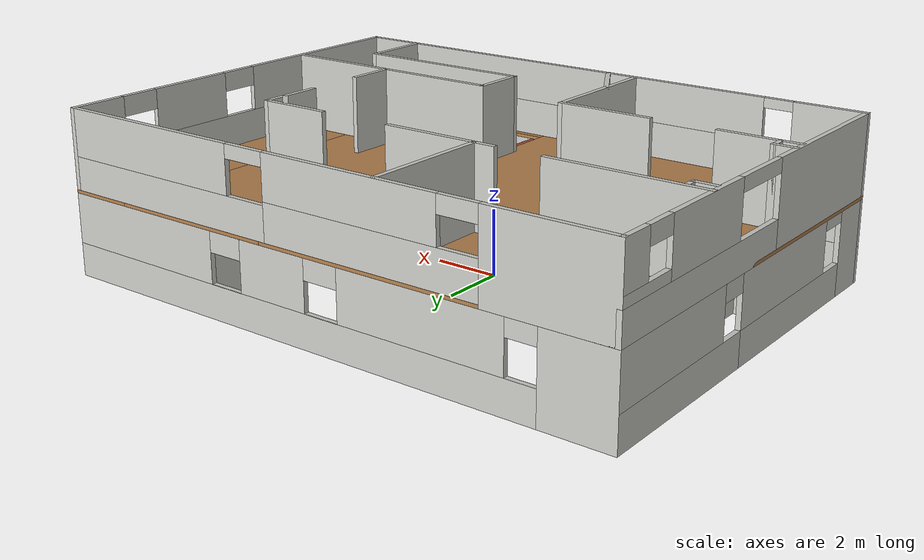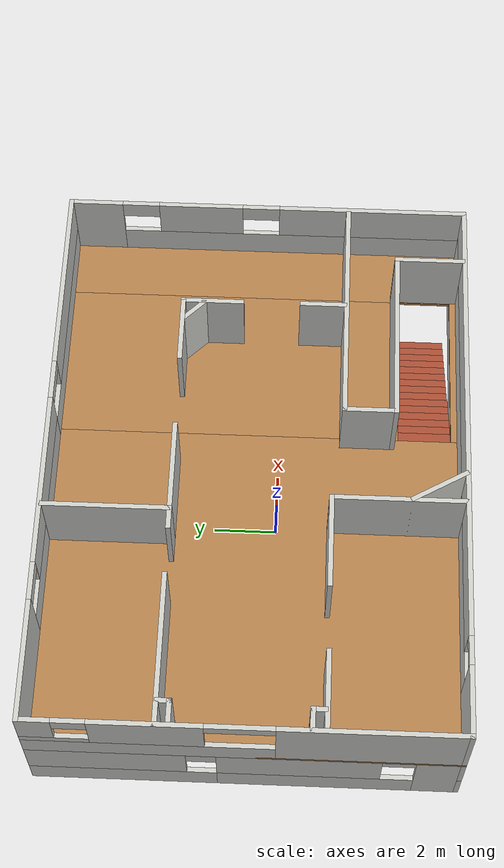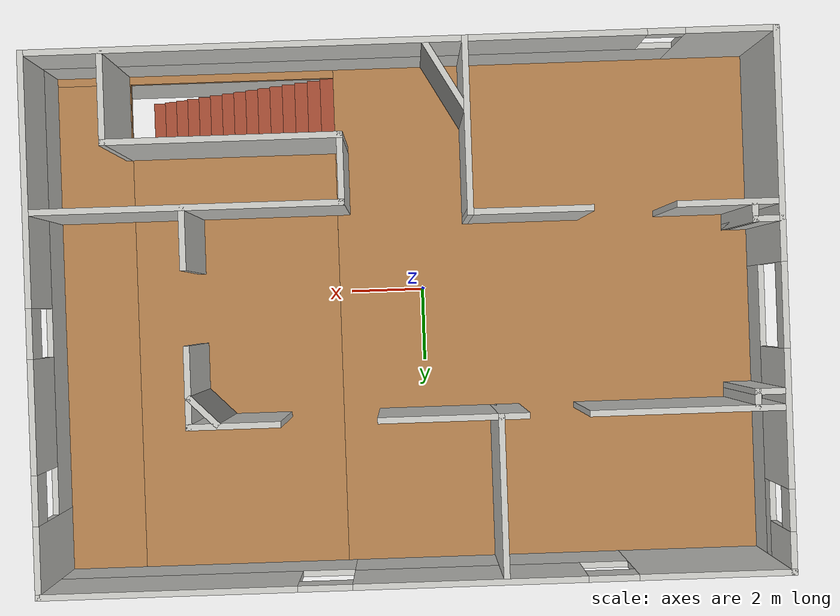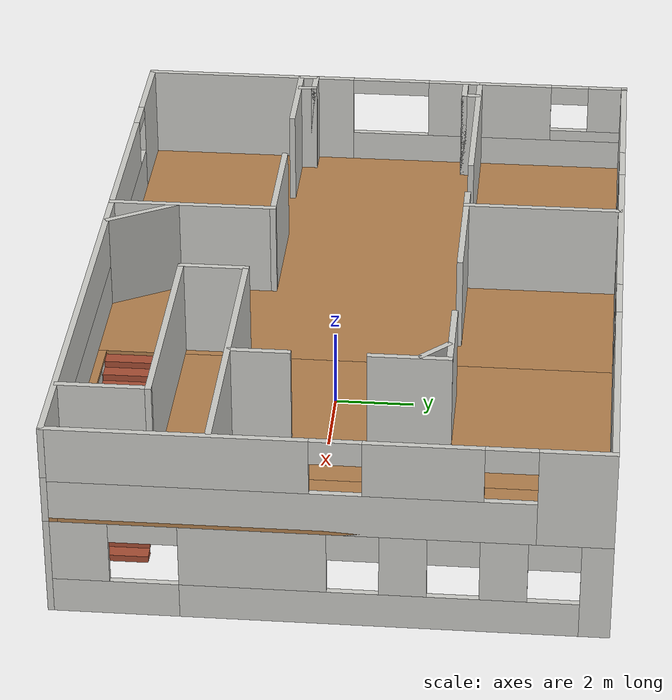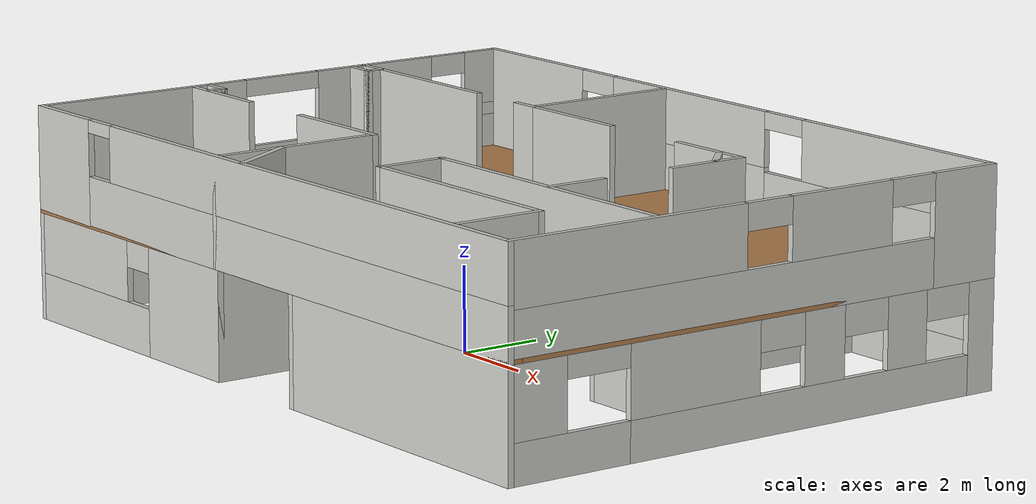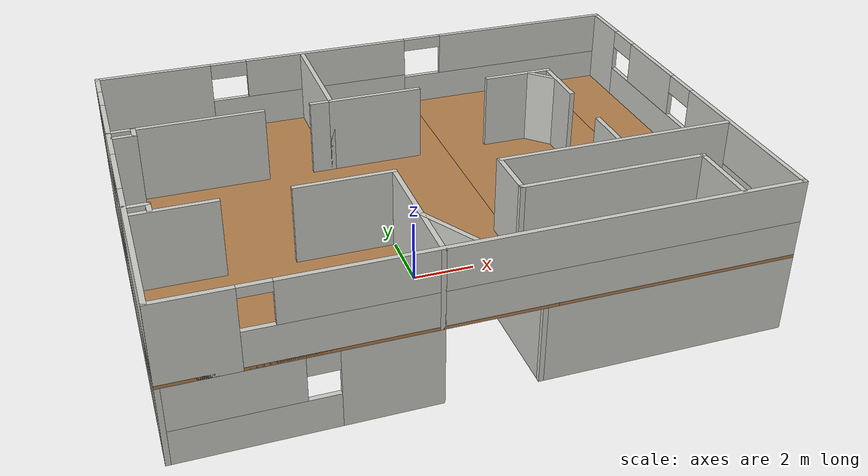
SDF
<?xml version='1.0'?>
<sdf version='1.6'>
  <model name='Indoor_Scenario1'>
    <pose frame=''>0.463179 0.653592 0 0 -0 0</pose>
    <link name='Floor_0'>
      <pose frame=''>-0 -0 2.5 0 -0 0</pose>
      <visual name='Floor_0_Visual_0'>
        <pose frame=''>-3.6411 0 0.05 0 -0 0</pose>
        <geometry>
          <box>
            <size>10.7178 13 0.1</size>
          </box>
        </geometry>
        <material>
          <script>
            <uri>file://media/materials/scripts/gazebo.material</uri>
            <name>Gazebo/Wood</name>
          </script>
          <ambient>1 1 1 1</ambient>
        </material>
        <meta>
          <layer>1</layer>
        </meta>
      </visual>
      <collision name='Floor_0_Collision_0'>
        <geometry>
          <box>
            <size>10.7178 13 0.1</size>
          </box>
        </geometry>
        <pose frame=''>-3.6411 0 0.05 0 -0 0</pose>
      </collision>
      <visual name='Floor_0_Visual_1'>
        <pose frame=''>5.3589 -6.32413 0.05 0 -0 0</pose>
        <geometry>
          <box>
            <size>7.2822 0.351742 0.1</size>
          </box>
        </geometry>
        <material>
          <script>
            <uri>file://media/materials/scripts/gazebo.material</uri>
            <name>Gazebo/Wood</name>
          </script>
          <ambient>1 1 1 1</ambient>
        </material>
        <meta>
          <layer>1</layer>
        </meta>
      </visual>
      <collision name='Floor_0_Collision_1'>
        <geometry>
          <box>
            <size>7.2822 0.351742 0.1</size>
          </box>
        </geometry>
        <pose frame=''>5.3589 -6.32413 0.05 0 -0 0</pose>
      </collision>
      <visual name='Floor_0_Visual_2'>
        <pose frame=''>7.97998 0.175871 0.05 0 -0 0</pose>
        <geometry>
          <box>
            <size>2.04005 12.6483 0.1</size>
          </box>
        </geometry>
        <material>
          <script>
            <uri>file://media/materials/scripts/gazebo.material</uri>
            <name>Gazebo/Wood</name>
          </script>
          <ambient>1 1 1 1</ambient>
        </material>
        <meta>
          <layer>1</layer>
        </meta>
      </visual>
      <collision name='Floor_0_Collision_2'>
        <geometry>
          <box>
            <size>2.04005 12.6483 0.1</size>
          </box>
        </geometry>
        <pose frame=''>7.97998 0.175871 0.05 0 -0 0</pose>
      </collision>
      <visual name='Floor_0_Visual_3'>
        <pose frame=''>4.33888 1.02587 0.05 0 -0 0</pose>
        <geometry>
          <box>
            <size>5.24215 10.9483 0.1</size>
          </box>
        </geometry>
        <material>
          <script>
            <uri>file://media/materials/scripts/gazebo.material</uri>
            <name>Gazebo/Wood</name>
          </script>
          <ambient>1 1 1 1</ambient>
        </material>
        <meta>
          <layer>1</layer>
        </meta>
      </visual>
      <collision name='Floor_0_Collision_3'>
        <geometry>
          <box>
            <size>5.24215 10.9483 0.1</size>
          </box>
        </geometry>
        <pose frame=''>4.33888 1.02587 0.05 0 -0 0</pose>
      </collision>
    </link>
    <link name='Stairs_0'>
      <visual name='Stairs_0_Visual_0'>
        <pose frame=''>6.78522 -5.29826 0.083333 0 -0 -1.5708</pose>
        <geometry>
          <box>
            <size>1.7 0.349477 0.166667</size>
          </box>
        </geometry>
        <material>
          <script>
            <uri>file://media/materials/scripts/gazebo.material</uri>
            <name>Gazebo/Bricks</name>
          </script>
          <ambient>1 1 1 1</ambient>
        </material>
        <meta>
          <layer>0</layer>
        </meta>
      </visual>
      <collision name='Stairs_0_Collision_0'>
        <geometry>
          <box>
            <size>1.7 0.349477 0.166667</size>
          </box>
        </geometry>
        <pose frame=''>6.78522 -5.29826 0.083333 0 -0 -1.5708</pose>
      </collision>
      <visual name='Stairs_0_Visual_1'>
        <pose frame=''>6.43574 -5.29826 0.25 0 -0 -1.5708</pose>
        <geometry>
          <box>
            <size>1.7 0.349477 0.166667</size>
          </box>
        </geometry>
        <material>
          <script>
            <uri>file://media/materials/scripts/gazebo.material</uri>
            <name>Gazebo/Bricks</name>
          </script>
          <ambient>1 1 1 1</ambient>
        </material>
        <meta>
          <layer>0</layer>
        </meta>
      </visual>
      <collision name='Stairs_0_Collision_1'>
        <geometry>
          <box>
            <size>1.7 0.349477 0.166667</size>
          </box>
        </geometry>
        <pose frame=''>6.43574 -5.29826 0.25 0 -0 -1.5708</pose>
      </collision>
      <visual name='Stairs_0_Visual_2'>
        <pose frame=''>6.08626 -5.29826 0.416667 0 -0 -1.5708</pose>
        <geometry>
          <box>
            <size>1.7 0.349477 0.166667</size>
          </box>
        </geometry>
        <material>
          <script>
            <uri>file://media/materials/scripts/gazebo.material</uri>
            <name>Gazebo/Bricks</name>
          </script>
          <ambient>1 1 1 1</ambient>
        </material>
        <meta>
          <layer>0</layer>
        </meta>
      </visual>
      <collision name='Stairs_0_Collision_2'>
        <geometry>
          <box>
            <size>1.7 0.349477 0.166667</size>
          </box>
        </geometry>
        <pose frame=''>6.08626 -5.29826 0.416667 0 -0 -1.5708</pose>
      </collision>
      <visual name='Stairs_0_Visual_3'>
        <pose frame=''>5.73679 -5.29826 0.583333 0 -0 -1.5708</pose>
        <geometry>
          <box>
            <size>1.7 0.349477 0.166667</size>
          </box>
        </geometry>
        <material>
          <script>
            <uri>file://media/materials/scripts/gazebo.material</uri>
            <name>Gazebo/Bricks</name>
          </script>
          <ambient>1 1 1 1</ambient>
        </material>
        <meta>
          <layer>0</layer>
        </meta>
      </visual>
      <collision name='Stairs_0_Collision_3'>
        <geometry>
          <box>
            <size>1.7 0.349477 0.166667</size>
          </box>
        </geometry>
        <pose frame=''>5.73679 -5.29826 0.583333 0 -0 -1.5708</pose>
      </collision>
      <visual name='Stairs_0_Visual_4'>
        <pose frame=''>5.38731 -5.29826 0.75 0 -0 -1.5708</pose>
        <geometry>
          <box>
            <size>1.7 0.349477 0.166667</size>
          </box>
        </geometry>
        <material>
          <script>
            <uri>file://media/materials/scripts/gazebo.material</uri>
            <name>Gazebo/Bricks</name>
          </script>
          <ambient>1 1 1 1</ambient>
        </material>
        <meta>
          <layer>0</layer>
        </meta>
      </visual>
      <collision name='Stairs_0_Collision_4'>
        <geometry>
          <box>
            <size>1.7 0.349477 0.166667</size>
          </box>
        </geometry>
        <pose frame=''>5.38731 -5.29826 0.75 0 -0 -1.5708</pose>
      </collision>
      <visual name='Stairs_0_Visual_5'>
        <pose frame=''>5.03783 -5.29826 0.916667 0 -0 -1.5708</pose>
        <geometry>
          <box>
            <size>1.7 0.349477 0.166667</size>
          </box>
        </geometry>
        <material>
          <script>
            <uri>file://media/materials/scripts/gazebo.material</uri>
            <name>Gazebo/Bricks</name>
          </script>
          <ambient>1 1 1 1</ambient>
        </material>
        <meta>
          <layer>0</layer>
        </meta>
      </visual>
      <collision name='Stairs_0_Collision_5'>
        <geometry>
          <box>
            <size>1.7 0.349477 0.166667</size>
          </box>
        </geometry>
        <pose frame=''>5.03783 -5.29826 0.916667 0 -0 -1.5708</pose>
      </collision>
      <visual name='Stairs_0_Visual_6'>
        <pose frame=''>4.68835 -5.29826 1.08333 0 -0 -1.5708</pose>
        <geometry>
          <box>
            <size>1.7 0.349477 0.166667</size>
          </box>
        </geometry>
        <material>
          <script>
            <uri>file://media/materials/scripts/gazebo.material</uri>
            <name>Gazebo/Bricks</name>
          </script>
          <ambient>1 1 1 1</ambient>
        </material>
        <meta>
          <layer>0</layer>
        </meta>
      </visual>
      <collision name='Stairs_0_Collision_6'>
        <geometry>
          <box>
            <size>1.7 0.349477 0.166667</size>
          </box>
        </geometry>
        <pose frame=''>4.68835 -5.29826 1.08333 0 -0 -1.5708</pose>
      </collision>
      <visual name='Stairs_0_Visual_7'>
        <pose frame=''>4.33888 -5.29826 1.25 0 -0 -1.5708</pose>
        <geometry>
          <box>
            <size>1.7 0.349477 0.166667</size>
          </box>
        </geometry>
        <material>
          <script>
            <uri>file://media/materials/scripts/gazebo.material</uri>
            <name>Gazebo/Bricks</name>
          </script>
          <ambient>1 1 1 1</ambient>
        </material>
        <meta>
          <layer>0</layer>
        </meta>
      </visual>
      <collision name='Stairs_0_Collision_7'>
        <geometry>
          <box>
            <size>1.7 0.349477 0.166667</size>
          </box>
        </geometry>
        <pose frame=''>4.33888 -5.29826 1.25 0 -0 -1.5708</pose>
      </collision>
      <visual name='Stairs_0_Visual_8'>
        <pose frame=''>3.9894 -5.29826 1.41667 0 -0 -1.5708</pose>
        <geometry>
          <box>
            <size>1.7 0.349477 0.166667</size>
          </box>
        </geometry>
        <material>
          <script>
            <uri>file://media/materials/scripts/gazebo.material</uri>
            <name>Gazebo/Bricks</name>
          </script>
          <ambient>1 1 1 1</ambient>
        </material>
        <meta>
          <layer>0</layer>
        </meta>
      </visual>
      <collision name='Stairs_0_Collision_8'>
        <geometry>
          <box>
            <size>1.7 0.349477 0.166667</size>
          </box>
        </geometry>
        <pose frame=''>3.9894 -5.29826 1.41667 0 -0 -1.5708</pose>
      </collision>
      <visual name='Stairs_0_Visual_9'>
        <pose frame=''>3.63992 -5.29826 1.58333 0 -0 -1.5708</pose>
        <geometry>
          <box>
            <size>1.7 0.349477 0.166667</size>
          </box>
        </geometry>
        <material>
          <script>
            <uri>file://media/materials/scripts/gazebo.material</uri>
            <name>Gazebo/Bricks</name>
          </script>
          <ambient>1 1 1 1</ambient>
        </material>
        <meta>
          <layer>0</layer>
        </meta>
      </visual>
      <collision name='Stairs_0_Collision_9'>
        <geometry>
          <box>
            <size>1.7 0.349477 0.166667</size>
          </box>
        </geometry>
        <pose frame=''>3.63992 -5.29826 1.58333 0 -0 -1.5708</pose>
      </collision>
      <visual name='Stairs_0_Visual_10'>
        <pose frame=''>3.29045 -5.29826 1.75 0 -0 -1.5708</pose>
        <geometry>
          <box>
            <size>1.7 0.349477 0.166667</size>
          </box>
        </geometry>
        <material>
          <script>
            <uri>file://media/materials/scripts/gazebo.material</uri>
            <name>Gazebo/Bricks</name>
          </script>
          <ambient>1 1 1 1</ambient>
        </material>
        <meta>
          <layer>0</layer>
        </meta>
      </visual>
      <collision name='Stairs_0_Collision_10'>
        <geometry>
          <box>
            <size>1.7 0.349477 0.166667</size>
          </box>
        </geometry>
        <pose frame=''>3.29045 -5.29826 1.75 0 -0 -1.5708</pose>
      </collision>
      <visual name='Stairs_0_Visual_11'>
        <pose frame=''>2.94097 -5.29826 1.91667 0 -0 -1.5708</pose>
        <geometry>
          <box>
            <size>1.7 0.349477 0.166667</size>
          </box>
        </geometry>
        <material>
          <script>
            <uri>file://media/materials/scripts/gazebo.material</uri>
            <name>Gazebo/Bricks</name>
          </script>
          <ambient>1 1 1 1</ambient>
        </material>
        <meta>
          <layer>0</layer>
        </meta>
      </visual>
      <collision name='Stairs_0_Collision_11'>
        <geometry>
          <box>
            <size>1.7 0.349477 0.166667</size>
          </box>
        </geometry>
        <pose frame=''>2.94097 -5.29826 1.91667 0 -0 -1.5708</pose>
      </collision>
      <visual name='Stairs_0_Visual_12'>
        <pose frame=''>2.59149 -5.29826 2.08333 0 -0 -1.5708</pose>
        <geometry>
          <box>
            <size>1.7 0.349477 0.166667</size>
          </box>
        </geometry>
        <material>
          <script>
            <uri>file://media/materials/scripts/gazebo.material</uri>
            <name>Gazebo/Bricks</name>
          </script>
          <ambient>1 1 1 1</ambient>
        </material>
        <meta>
          <layer>0</layer>
        </meta>
      </visual>
      <collision name='Stairs_0_Collision_12'>
        <geometry>
          <box>
            <size>1.7 0.349477 0.166667</size>
          </box>
        </geometry>
        <pose frame=''>2.59149 -5.29826 2.08333 0 -0 -1.5708</pose>
      </collision>
      <visual name='Stairs_0_Visual_13'>
        <pose frame=''>2.24202 -5.29826 2.25 0 -0 -1.5708</pose>
        <geometry>
          <box>
            <size>1.7 0.349477 0.166667</size>
          </box>
        </geometry>
        <material>
          <script>
            <uri>file://media/materials/scripts/gazebo.material</uri>
            <name>Gazebo/Bricks</name>
          </script>
          <ambient>1 1 1 1</ambient>
        </material>
        <meta>
          <layer>0</layer>
        </meta>
      </visual>
      <collision name='Stairs_0_Collision_13'>
        <geometry>
          <box>
            <size>1.7 0.349477 0.166667</size>
          </box>
        </geometry>
        <pose frame=''>2.24202 -5.29826 2.25 0 -0 -1.5708</pose>
      </collision>
      <visual name='Stairs_0_Visual_14'>
        <pose frame=''>1.89254 -5.29826 2.41667 0 -0 -1.5708</pose>
        <geometry>
          <box>
            <size>1.7 0.349477 0.166667</size>
          </box>
        </geometry>
        <material>
          <script>
            <uri>file://media/materials/scripts/gazebo.material</uri>
            <name>Gazebo/Bricks</name>
          </script>
          <ambient>1 1 1 1</ambient>
        </material>
        <meta>
          <layer>0</layer>
        </meta>
      </visual>
      <collision name='Stairs_0_Collision_14'>
        <geometry>
          <box>
            <size>1.7 0.349477 0.166667</size>
          </box>
        </geometry>
        <pose frame=''>1.89254 -5.29826 2.41667 0 -0 -1.5708</pose>
      </collision>
    </link>
    <link name='Wall_0'>
      <pose frame=''>-5.25 -6.425 0 0 -0 3.14159</pose>
      <visual name='Wall_0_Visual_0'>
        <pose frame=''>-2.33577 0 1.25 0 -0 0</pose>
        <geometry>
          <box>
            <size>2.82847 0.15 2.5</size>
          </box>
        </geometry>
        <material>
          <script>
            <uri>file://media/materials/scripts/gazebo.material</uri>
            <name>Gazebo/CeilingTiled</name>
          </script>
          <ambient>0.647059 0.505882 0.309804 1</ambient>
        </material>
        <meta>
          <layer>0</layer>
        </meta>
      </visual>
      <collision name='Wall_0_Collision_0'>
        <geometry>
          <box>
            <size>2.82847 0.15 2.5</size>
          </box>
        </geometry>
        <pose frame=''>-2.33577 0 1.25 0 -0 0</pose>
      </collision>
      <visual name='Wall_0_Visual_1'>
        <pose frame=''>1.41423 0 0.55 0 -0 0</pose>
        <geometry>
          <box>
            <size>4.67153 0.15 1.1</size>
          </box>
        </geometry>
        <material>
          <script>
            <uri>file://media/materials/scripts/gazebo.material</uri>
            <name>Gazebo/CeilingTiled</name>
          </script>
          <ambient>0.647059 0.505882 0.309804 1</ambient>
        </material>
        <meta>
          <layer>0</layer>
        </meta>
      </visual>
      <collision name='Wall_0_Collision_1'>
        <geometry>
          <box>
            <size>4.67153 0.15 1.1</size>
          </box>
        </geometry>
        <pose frame=''>1.41423 0 0.55 0 -0 0</pose>
      </collision>
      <visual name='Wall_0_Visual_2'>
        <pose frame=''>1.86423 0 1.8 0 -0 0</pose>
        <geometry>
          <box>
            <size>3.77153 0.15 1.4</size>
          </box>
        </geometry>
        <material>
          <script>
            <uri>file://media/materials/scripts/gazebo.material</uri>
            <name>Gazebo/CeilingTiled</name>
          </script>
          <ambient>0.647059 0.505882 0.309804 1</ambient>
        </material>
        <meta>
          <layer>0</layer>
        </meta>
      </visual>
      <collision name='Wall_0_Collision_2'>
        <geometry>
          <box>
            <size>3.77153 0.15 1.4</size>
          </box>
        </geometry>
        <pose frame=''>1.86423 0 1.8 0 -0 0</pose>
      </collision>
      <visual name='Wall_0_Visual_3'>
        <pose frame=''>-0.471532 0 2.2 0 -0 0</pose>
        <geometry>
          <box>
            <size>0.9 0.15 0.6</size>
          </box>
        </geometry>
        <material>
          <script>
            <uri>file://media/materials/scripts/gazebo.material</uri>
            <name>Gazebo/CeilingTiled</name>
          </script>
          <ambient>0.647059 0.505882 0.309804 1</ambient>
        </material>
        <meta>
          <layer>0</layer>
        </meta>
      </visual>
      <collision name='Wall_0_Collision_3'>
        <geometry>
          <box>
            <size>0.9 0.15 0.6</size>
          </box>
        </geometry>
        <pose frame=''>-0.471532 0 2.2 0 -0 0</pose>
      </collision>
    </link>
    <link name='Wall_1'>
      <pose frame=''>-8.925 -0 0 0 -0 1.5708</pose>
      <visual name='Wall_1_Visual_0'>
        <pose frame=''>-5.77686 0 1.25 0 -0 0</pose>
        <geometry>
          <box>
            <size>1.44627 0.15 2.5</size>
          </box>
        </geometry>
        <material>
          <script>
            <uri>file://media/materials/scripts/gazebo.material</uri>
            <name>Gazebo/CeilingTiled</name>
          </script>
          <ambient>0.647059 0.505882 0.309804 1</ambient>
        </material>
        <meta>
          <layer>0</layer>
        </meta>
      </visual>
      <collision name='Wall_1_Collision_0'>
        <geometry>
          <box>
            <size>1.44627 0.15 2.5</size>
          </box>
        </geometry>
        <pose frame=''>-5.77686 0 1.25 0 -0 0</pose>
      </collision>
      <visual name='Wall_1_Visual_1'>
        <pose frame=''>-2.10736 0 0.5 0 -0 0</pose>
        <geometry>
          <box>
            <size>5.89273 0.15 1</size>
          </box>
        </geometry>
        <material>
          <script>
            <uri>file://media/materials/scripts/gazebo.material</uri>
            <name>Gazebo/CeilingTiled</name>
          </script>
          <ambient>0.647059 0.505882 0.309804 1</ambient>
        </material>
        <meta>
          <layer>0</layer>
        </meta>
      </visual>
      <collision name='Wall_1_Collision_1'>
        <geometry>
          <box>
            <size>5.89273 0.15 1</size>
          </box>
        </geometry>
        <pose frame=''>-2.10736 0 0.5 0 -0 0</pose>
      </collision>
      <visual name='Wall_1_Visual_2'>
        <pose frame=''>3.6695 0 0.5 0 -0 0</pose>
        <geometry>
          <box>
            <size>5.66099 0.15 1</size>
          </box>
        </geometry>
        <material>
          <script>
            <uri>file://media/materials/scripts/gazebo.material</uri>
            <name>Gazebo/CeilingTiled</name>
          </script>
          <ambient>0.647059 0.505882 0.309804 1</ambient>
        </material>
        <meta>
          <layer>0</layer>
        </meta>
      </visual>
      <collision name='Wall_1_Collision_2'>
        <geometry>
          <box>
            <size>5.66099 0.15 1</size>
          </box>
        </geometry>
        <pose frame=''>3.6695 0 0.5 0 -0 0</pose>
      </collision>
      <visual name='Wall_1_Visual_3'>
        <pose frame=''>4.1195 0 1.75 0 -0 0</pose>
        <geometry>
          <box>
            <size>4.76099 0.15 1.5</size>
          </box>
        </geometry>
        <material>
          <script>
            <uri>file://media/materials/scripts/gazebo.material</uri>
            <name>Gazebo/CeilingTiled</name>
          </script>
          <ambient>0.647059 0.505882 0.309804 1</ambient>
        </material>
        <meta>
          <layer>0</layer>
        </meta>
      </visual>
      <collision name='Wall_1_Collision_3'>
        <geometry>
          <box>
            <size>4.76099 0.15 1.5</size>
          </box>
        </geometry>
        <pose frame=''>4.1195 0 1.75 0 -0 0</pose>
      </collision>
      <visual name='Wall_1_Visual_4'>
        <pose frame=''>-1.60736 0 1.75 0 -0 0</pose>
        <geometry>
          <box>
            <size>4.89273 0.15 1.5</size>
          </box>
        </geometry>
        <material>
          <script>
            <uri>file://media/materials/scripts/gazebo.material</uri>
            <name>Gazebo/CeilingTiled</name>
          </script>
          <ambient>0.647059 0.505882 0.309804 1</ambient>
        </material>
        <meta>
          <layer>0</layer>
        </meta>
      </visual>
      <collision name='Wall_1_Collision_4'>
        <geometry>
          <box>
            <size>4.89273 0.15 1.5</size>
          </box>
        </geometry>
        <pose frame=''>-1.60736 0 1.75 0 -0 0</pose>
      </collision>
      <visual name='Wall_1_Visual_5'>
        <pose frame=''>-1.60736 0 1.75 0 -0 0</pose>
        <geometry>
          <box>
            <size>4.89273 0.15 1.5</size>
          </box>
        </geometry>
        <material>
          <script>
            <uri>file://media/materials/scripts/gazebo.material</uri>
            <name>Gazebo/CeilingTiled</name>
          </script>
          <ambient>0.647059 0.505882 0.309804 1</ambient>
        </material>
        <meta>
          <layer>0</layer>
        </meta>
      </visual>
      <collision name='Wall_1_Collision_5'>
        <geometry>
          <box>
            <size>4.89273 0.15 1.5</size>
          </box>
        </geometry>
        <pose frame=''>-1.60736 0 1.75 0 -0 0</pose>
      </collision>
      <visual name='Wall_1_Visual_6'>
        <pose frame=''>1.28901 0 2.25 0 -0 0</pose>
        <geometry>
          <box>
            <size>0.9 0.15 0.5</size>
          </box>
        </geometry>
        <material>
          <script>
            <uri>file://media/materials/scripts/gazebo.material</uri>
            <name>Gazebo/CeilingTiled</name>
          </script>
          <ambient>0.647059 0.505882 0.309804 1</ambient>
        </material>
        <meta>
          <layer>0</layer>
        </meta>
      </visual>
      <collision name='Wall_1_Collision_6'>
        <geometry>
          <box>
            <size>0.9 0.15 0.5</size>
          </box>
        </geometry>
        <pose frame=''>1.28901 0 2.25 0 -0 0</pose>
      </collision>
      <visual name='Wall_1_Visual_7'>
        <pose frame=''>1.28901 0 2.25 0 -0 0</pose>
        <geometry>
          <box>
            <size>0.9 0.15 0.5</size>
          </box>
        </geometry>
        <material>
          <script>
            <uri>file://media/materials/scripts/gazebo.material</uri>
            <name>Gazebo/CeilingTiled</name>
          </script>
          <ambient>0.647059 0.505882 0.309804 1</ambient>
        </material>
        <meta>
          <layer>0</layer>
        </meta>
      </visual>
      <collision name='Wall_1_Collision_7'>
        <geometry>
          <box>
            <size>0.9 0.15 0.5</size>
          </box>
        </geometry>
        <pose frame=''>1.28901 0 2.25 0 -0 0</pose>
      </collision>
      <visual name='Wall_1_Visual_8'>
        <pose frame=''>-4.55373 0 2.35 0 -0 0</pose>
        <geometry>
          <box>
            <size>1 0.15 0.3</size>
          </box>
        </geometry>
        <material>
          <script>
            <uri>file://media/materials/scripts/gazebo.material</uri>
            <name>Gazebo/CeilingTiled</name>
          </script>
          <ambient>0.647059 0.505882 0.309804 1</ambient>
        </material>
        <meta>
          <layer>0</layer>
        </meta>
      </visual>
      <collision name='Wall_1_Collision_8'>
        <geometry>
          <box>
            <size>1 0.15 0.3</size>
          </box>
        </geometry>
        <pose frame=''>-4.55373 0 2.35 0 -0 0</pose>
      </collision>
    </link>
    <link name='Wall_10'>
      <collision name='Wall_10_Collision'>
        <geometry>
          <box>
            <size>4.25 0.15 2.5</size>
          </box>
        </geometry>
        <pose frame=''>0 0 1.25 0 -0 0</pose>
      </collision>
      <visual name='Wall_10_Visual'>
        <pose frame=''>0 0 1.25 0 -0 0</pose>
        <geometry>
          <box>
            <size>4.25 0.15 2.5</size>
          </box>
        </geometry>
        <material>
          <script>
            <uri>file://media/materials/scripts/gazebo.material</uri>
            <name>Gazebo/CeilingTiled</name>
          </script>
          <ambient>0.647059 0.505882 0.309804 1</ambient>
        </material>
        <meta>
          <layer>0</layer>
        </meta>
      </visual>
      <pose frame=''>-1.575 -4.375 0 0 -0 1.5708</pose>
    </link>
    <link name='Wall_101'>
      <collision name='Wall_101_Collision'>
        <geometry>
          <box>
            <size>0.75 0.15 2.5</size>
          </box>
        </geometry>
        <pose frame=''>0 0 1.25 0 -0 0</pose>
      </collision>
      <visual name='Wall_101_Visual'>
        <pose frame=''>0 0 1.25 0 -0 0</pose>
        <geometry>
          <box>
            <size>0.75 0.15 2.5</size>
          </box>
        </geometry>
        <material>
          <script>
            <uri>file://media/materials/scripts/gazebo.material</uri>
            <name>Gazebo/CeilingTiled</name>
          </script>
          <ambient>1 1 1 1</ambient>
        </material>
        <meta>
          <layer>1</layer>
        </meta>
      </visual>
      <pose frame=''>-8.58941 -1.93229 2.5 0 -0 0</pose>
    </link>
    <link name='Wall_102'>
      <collision name='Wall_102_Collision'>
        <geometry>
          <box>
            <size>0.5 0.15 2.5</size>
          </box>
        </geometry>
        <pose frame=''>0 0 1.25 0 -0 0</pose>
      </collision>
      <visual name='Wall_102_Visual'>
        <pose frame=''>0 0 1.25 0 -0 0</pose>
        <geometry>
          <box>
            <size>0.5 0.15 2.5</size>
          </box>
        </geometry>
        <material>
          <script>
            <uri>file://media/materials/scripts/gazebo.material</uri>
            <name>Gazebo/CeilingTiled</name>
          </script>
          <ambient>1 1 1 1</ambient>
        </material>
        <meta>
          <layer>1</layer>
        </meta>
      </visual>
      <pose frame=''>-8.28941 -2.10729 2.5 0 -0 -1.5708</pose>
    </link>
    <link name='Wall_12'>
      <collision name='Wall_12_Collision'>
        <geometry>
          <box>
            <size>2 0.15 2.5</size>
          </box>
        </geometry>
        <pose frame=''>0 0 1.25 0 -0 0</pose>
      </collision>
      <visual name='Wall_12_Visual'>
        <pose frame=''>0 0 1.25 0 -0 0</pose>
        <geometry>
          <box>
            <size>2 0.15 2.5</size>
          </box>
        </geometry>
        <material>
          <script>
            <uri>file://media/materials/scripts/gazebo.material</uri>
            <name>Gazebo/CeilingTiled</name>
          </script>
          <ambient>1 1 1 1</ambient>
        </material>
        <meta>
          <layer>0</layer>
        </meta>
      </visual>
      <pose frame=''>-2.5 -2.325 0 0 -0 3.14159</pose>
    </link>
    <link name='Wall_14'>
      <collision name='Wall_14_Collision'>
        <geometry>
          <box>
            <size>3.5 0.15 2.5</size>
          </box>
        </geometry>
        <pose frame=''>0 0 1.25 0 -0 0</pose>
      </collision>
      <visual name='Wall_14_Visual'>
        <pose frame=''>0 0 1.25 0 -0 0</pose>
        <geometry>
          <box>
            <size>3.5 0.15 2.5</size>
          </box>
        </geometry>
        <material>
          <script>
            <uri>file://media/materials/scripts/gazebo.material</uri>
            <name>Gazebo/CeilingTiled</name>
          </script>
          <ambient>1 1 1 1</ambient>
        </material>
        <meta>
          <layer>0</layer>
        </meta>
      </visual>
      <pose frame=''>-7.19556 -2.34297 0 0 -0 0</pose>
    </link>
    <link name='Wall_19'>
      <collision name='Wall_19_Collision'>
        <geometry>
          <box>
            <size>0.75 0.15 2.5</size>
          </box>
        </geometry>
        <pose frame=''>0 0 1.25 0 -0 0</pose>
      </collision>
      <visual name='Wall_19_Visual'>
        <pose frame=''>0 0 1.25 0 -0 0</pose>
        <geometry>
          <box>
            <size>0.75 0.15 2.5</size>
          </box>
        </geometry>
        <material>
          <script>
            <uri>file://media/materials/scripts/gazebo.material</uri>
            <name>Gazebo/CeilingTiled</name>
          </script>
          <ambient>1 1 1 1</ambient>
        </material>
        <meta>
          <layer>0</layer>
        </meta>
      </visual>
      <pose frame=''>1.67467 -4.10793 0 0 -0 -2.61799</pose>
    </link>
    <link name='Wall_2'>
      <pose frame=''>-0 6.425 0 0 -0 0</pose>
      <visual name='Wall_2_Visual_0'>
        <pose frame=''>-7.94017 0 1.25 0 -0 0</pose>
        <geometry>
          <box>
            <size>2.11966 0.15 2.5</size>
          </box>
        </geometry>
        <material>
          <script>
            <uri>file://media/materials/scripts/gazebo.material</uri>
            <name>Gazebo/CeilingTiled</name>
          </script>
          <ambient>0.647059 0.505882 0.309804 1</ambient>
        </material>
        <meta>
          <layer>0</layer>
        </meta>
      </visual>
      <collision name='Wall_2_Collision_0'>
        <geometry>
          <box>
            <size>2.11966 0.15 2.5</size>
          </box>
        </geometry>
        <pose frame=''>-7.94017 0 1.25 0 -0 0</pose>
      </collision>
      <visual name='Wall_2_Visual_1'>
        <pose frame=''>1.05983 0 0.5 0 -0 0</pose>
        <geometry>
          <box>
            <size>15.8803 0.15 1</size>
          </box>
        </geometry>
        <material>
          <script>
            <uri>file://media/materials/scripts/gazebo.material</uri>
            <name>Gazebo/CeilingTiled</name>
          </script>
          <ambient>0.647059 0.505882 0.309804 1</ambient>
        </material>
        <meta>
          <layer>0</layer>
        </meta>
      </visual>
      <collision name='Wall_2_Collision_1'>
        <geometry>
          <box>
            <size>15.8803 0.15 1</size>
          </box>
        </geometry>
        <pose frame=''>1.05983 0 0.5 0 -0 0</pose>
      </collision>
      <visual name='Wall_2_Visual_2'>
        <pose frame=''>-3.45191 0 1.75 0 -0 0</pose>
        <geometry>
          <box>
            <size>5.05687 0.15 1.5</size>
          </box>
        </geometry>
        <material>
          <script>
            <uri>file://media/materials/scripts/gazebo.material</uri>
            <name>Gazebo/CeilingTiled</name>
          </script>
          <ambient>0.647059 0.505882 0.309804 1</ambient>
        </material>
        <meta>
          <layer>0</layer>
        </meta>
      </visual>
      <collision name='Wall_2_Collision_2'>
        <geometry>
          <box>
            <size>5.05687 0.15 1.5</size>
          </box>
        </geometry>
        <pose frame=''>-3.45191 0 1.75 0 -0 0</pose>
      </collision>
      <visual name='Wall_2_Visual_3'>
        <pose frame=''>1.30899 0 1.75 0 -0 0</pose>
        <geometry>
          <box>
            <size>2.26492 0.15 1.5</size>
          </box>
        </geometry>
        <material>
          <script>
            <uri>file://media/materials/scripts/gazebo.material</uri>
            <name>Gazebo/CeilingTiled</name>
          </script>
          <ambient>0.647059 0.505882 0.309804 1</ambient>
        </material>
        <meta>
          <layer>0</layer>
        </meta>
      </visual>
      <collision name='Wall_2_Collision_3'>
        <geometry>
          <box>
            <size>2.26492 0.15 1.5</size>
          </box>
        </geometry>
        <pose frame=''>1.30899 0 1.75 0 -0 0</pose>
      </collision>
      <visual name='Wall_2_Visual_4'>
        <pose frame=''>6.27072 0 1.75 0 -0 0</pose>
        <geometry>
          <box>
            <size>5.45855 0.15 1.5</size>
          </box>
        </geometry>
        <material>
          <script>
            <uri>file://media/materials/scripts/gazebo.material</uri>
            <name>Gazebo/CeilingTiled</name>
          </script>
          <ambient>0.647059 0.505882 0.309804 1</ambient>
        </material>
        <meta>
          <layer>0</layer>
        </meta>
      </visual>
      <collision name='Wall_2_Collision_4'>
        <geometry>
          <box>
            <size>5.45855 0.15 1.5</size>
          </box>
        </geometry>
        <pose frame=''>6.27072 0 1.75 0 -0 0</pose>
      </collision>
      <visual name='Wall_2_Visual_5'>
        <pose frame=''>-0.373475 0 1 0 -0 0</pose>
        <geometry>
          <box>
            <size>1.1 0.15 0.01</size>
          </box>
        </geometry>
        <material>
          <script>
            <uri>file://media/materials/scripts/gazebo.material</uri>
            <name>Gazebo/CeilingTiled</name>
          </script>
          <ambient>0.647059 0.505882 0.309804 1</ambient>
        </material>
        <meta>
          <layer>0</layer>
        </meta>
      </visual>
      <collision name='Wall_2_Collision_5'>
        <geometry>
          <box>
            <size>1.1 0.15 0.01</size>
          </box>
        </geometry>
        <pose frame=''>-0.373475 0 1 0 -0 0</pose>
      </collision>
      <visual name='Wall_2_Visual_6'>
        <pose frame=''>2.99145 0 1 0 -0 0</pose>
        <geometry>
          <box>
            <size>1.1 0.15 0.01</size>
          </box>
        </geometry>
        <material>
          <script>
            <uri>file://media/materials/scripts/gazebo.material</uri>
            <name>Gazebo/CeilingTiled</name>
          </script>
          <ambient>0.647059 0.505882 0.309804 1</ambient>
        </material>
        <meta>
          <layer>0</layer>
        </meta>
      </visual>
      <collision name='Wall_2_Collision_6'>
        <geometry>
          <box>
            <size>1.1 0.15 0.01</size>
          </box>
        </geometry>
        <pose frame=''>2.99145 0 1 0 -0 0</pose>
      </collision>
      <visual name='Wall_2_Visual_7'>
        <pose frame=''>-0.373475 0 2.2 0 -0 0</pose>
        <geometry>
          <box>
            <size>1.1 0.15 0.6</size>
          </box>
        </geometry>
        <material>
          <script>
            <uri>file://media/materials/scripts/gazebo.material</uri>
            <name>Gazebo/CeilingTiled</name>
          </script>
          <ambient>0.647059 0.505882 0.309804 1</ambient>
        </material>
        <meta>
          <layer>0</layer>
        </meta>
      </visual>
      <collision name='Wall_2_Collision_7'>
        <geometry>
          <box>
            <size>1.1 0.15 0.6</size>
          </box>
        </geometry>
        <pose frame=''>-0.373475 0 2.2 0 -0 0</pose>
      </collision>
      <visual name='Wall_2_Visual_8'>
        <pose frame=''>2.99145 0 2.2 0 -0 0</pose>
        <geometry>
          <box>
            <size>1.1 0.15 0.6</size>
          </box>
        </geometry>
        <material>
          <script>
            <uri>file://media/materials/scripts/gazebo.material</uri>
            <name>Gazebo/CeilingTiled</name>
          </script>
          <ambient>0.647059 0.505882 0.309804 1</ambient>
        </material>
        <meta>
          <layer>0</layer>
        </meta>
      </visual>
      <collision name='Wall_2_Collision_8'>
        <geometry>
          <box>
            <size>1.1 0.15 0.6</size>
          </box>
        </geometry>
        <pose frame=''>2.99145 0 2.2 0 -0 0</pose>
      </collision>
      <visual name='Wall_2_Visual_9'>
        <pose frame=''>-6.43034 0 2.25 0 -0 0</pose>
        <geometry>
          <box>
            <size>0.9 0.15 0.5</size>
          </box>
        </geometry>
        <material>
          <script>
            <uri>file://media/materials/scripts/gazebo.material</uri>
            <name>Gazebo/CeilingTiled</name>
          </script>
          <ambient>0.647059 0.505882 0.309804 1</ambient>
        </material>
        <meta>
          <layer>0</layer>
        </meta>
      </visual>
      <collision name='Wall_2_Collision_9'>
        <geometry>
          <box>
            <size>0.9 0.15 0.5</size>
          </box>
        </geometry>
        <pose frame=''>-6.43034 0 2.25 0 -0 0</pose>
      </collision>
    </link>
    <link name='Wall_23'>
      <collision name='Wall_23_Collision'>
        <geometry>
          <box>
            <size>4 0.15 2.5</size>
          </box>
        </geometry>
        <pose frame=''>0 0 1.25 0 -0 0</pose>
      </collision>
      <visual name='Wall_23_Visual'>
        <pose frame=''>0 0 1.25 0 -0 0</pose>
        <geometry>
          <box>
            <size>4 0.15 2.5</size>
          </box>
        </geometry>
        <material>
          <script>
            <uri>file://media/materials/scripts/gazebo.material</uri>
            <name>Gazebo/CeilingTiled</name>
          </script>
          <ambient>1 1 1 1</ambient>
        </material>
        <meta>
          <layer>0</layer>
        </meta>
      </visual>
      <pose frame=''>-2.14075 4.44918 0 0 -0 -1.5708</pose>
    </link>
    <link name='Wall_24'>
      <collision name='Wall_24_Collision'>
        <geometry>
          <box>
            <size>1.25 0.15 2.5</size>
          </box>
        </geometry>
        <pose frame=''>0 0 1.25 0 -0 0</pose>
      </collision>
      <visual name='Wall_24_Visual'>
        <pose frame=''>0 0 1.25 0 -0 0</pose>
        <geometry>
          <box>
            <size>1.25 0.15 2.5</size>
          </box>
        </geometry>
        <material>
          <script>
            <uri>file://media/materials/scripts/gazebo.material</uri>
            <name>Gazebo/CeilingTiled</name>
          </script>
          <ambient>1 1 1 1</ambient>
        </material>
        <meta>
          <layer>0</layer>
        </meta>
      </visual>
      <pose frame=''>-2.69075 2.52418 0 0 -0 3.14159</pose>
    </link>
    <link name='Wall_28'>
      <collision name='Wall_28_Collision'>
        <geometry>
          <box>
            <size>4 0.15 2.5</size>
          </box>
        </geometry>
        <pose frame=''>0 0 1.25 0 -0 0</pose>
      </collision>
      <visual name='Wall_28_Visual'>
        <pose frame=''>0 0 1.25 0 -0 0</pose>
        <geometry>
          <box>
            <size>4 0.15 2.5</size>
          </box>
        </geometry>
        <material>
          <script>
            <uri>file://media/materials/scripts/gazebo.material</uri>
            <name>Gazebo/CeilingTiled</name>
          </script>
          <ambient>1 1 1 1</ambient>
        </material>
        <meta>
          <layer>0</layer>
        </meta>
      </visual>
      <pose frame=''>-6.98364 2.52637 0 0 -0 0</pose>
    </link>
    <link name='Wall_3'>
      <pose frame=''>8.925 -0 0 0 -0 -1.5708</pose>
      <visual name='Wall_3_Visual_0'>
        <pose frame=''>-6.13698 0 1.25 0 -0 0</pose>
        <geometry>
          <box>
            <size>0.726032 0.15 2.5</size>
          </box>
        </geometry>
        <material>
          <script>
            <uri>file://media/materials/scripts/gazebo.material</uri>
            <name>Gazebo/CeilingTiled</name>
          </script>
          <ambient>0.647059 0.505882 0.309804 1</ambient>
        </material>
        <meta>
          <layer>0</layer>
        </meta>
      </visual>
      <collision name='Wall_3_Collision_0'>
        <geometry>
          <box>
            <size>0.726032 0.15 2.5</size>
          </box>
        </geometry>
        <pose frame=''>-6.13698 0 1.25 0 -0 0</pose>
      </collision>
      <visual name='Wall_3_Visual_1'>
        <pose frame=''>-1.17837 0 0.45 0 -0 0</pose>
        <geometry>
          <box>
            <size>9.1912 0.15 0.9</size>
          </box>
        </geometry>
        <material>
          <script>
            <uri>file://media/materials/scripts/gazebo.material</uri>
            <name>Gazebo/CeilingTiled</name>
          </script>
          <ambient>0.647059 0.505882 0.309804 1</ambient>
        </material>
        <meta>
          <layer>0</layer>
        </meta>
      </visual>
      <collision name='Wall_3_Collision_1'>
        <geometry>
          <box>
            <size>9.1912 0.15 0.9</size>
          </box>
        </geometry>
        <pose frame=''>-1.17837 0 0.45 0 -0 0</pose>
      </collision>
      <visual name='Wall_3_Visual_2'>
        <pose frame=''>4.95862 0 0.45 0 -0 0</pose>
        <geometry>
          <box>
            <size>3.08277 0.15 0.9</size>
          </box>
        </geometry>
        <material>
          <script>
            <uri>file://media/materials/scripts/gazebo.material</uri>
            <name>Gazebo/CeilingTiled</name>
          </script>
          <ambient>0.647059 0.505882 0.309804 1</ambient>
        </material>
        <meta>
          <layer>0</layer>
        </meta>
      </visual>
      <collision name='Wall_3_Collision_2'>
        <geometry>
          <box>
            <size>3.08277 0.15 0.9</size>
          </box>
        </geometry>
        <pose frame=''>4.95862 0 0.45 0 -0 0</pose>
      </collision>
      <visual name='Wall_3_Visual_3'>
        <pose frame=''>5.75862 0 1.7 0 -0 0</pose>
        <geometry>
          <box>
            <size>1.48277 0.15 1.6</size>
          </box>
        </geometry>
        <material>
          <script>
            <uri>file://media/materials/scripts/gazebo.material</uri>
            <name>Gazebo/CeilingTiled</name>
          </script>
          <ambient>0.647059 0.505882 0.309804 1</ambient>
        </material>
        <meta>
          <layer>0</layer>
        </meta>
      </visual>
      <collision name='Wall_3_Collision_3'>
        <geometry>
          <box>
            <size>1.48277 0.15 1.6</size>
          </box>
        </geometry>
        <pose frame=''>5.75862 0 1.7 0 -0 0</pose>
      </collision>
      <visual name='Wall_3_Visual_4'>
        <pose frame=''>-4.02683 0 1.7 0 -0 0</pose>
        <geometry>
          <box>
            <size>1.09427 0.15 1.6</size>
          </box>
        </geometry>
        <material>
          <script>
            <uri>file://media/materials/scripts/gazebo.material</uri>
            <name>Gazebo/CeilingTiled</name>
          </script>
          <ambient>0.647059 0.505882 0.309804 1</ambient>
        </material>
        <meta>
          <layer>0</layer>
        </meta>
      </visual>
      <collision name='Wall_3_Collision_4'>
        <geometry>
          <box>
            <size>1.09427 0.15 1.6</size>
          </box>
        </geometry>
        <pose frame=''>-4.02683 0 1.7 0 -0 0</pose>
      </collision>
      <visual name='Wall_3_Visual_5'>
        <pose frame=''>-1.73257 0 1.7 0 -0 0</pose>
        <geometry>
          <box>
            <size>1.09427 0.15 1.6</size>
          </box>
        </geometry>
        <material>
          <script>
            <uri>file://media/materials/scripts/gazebo.material</uri>
            <name>Gazebo/CeilingTiled</name>
          </script>
          <ambient>0.647059 0.505882 0.309804 1</ambient>
        </material>
        <meta>
          <layer>0</layer>
        </meta>
      </visual>
      <collision name='Wall_3_Collision_5'>
        <geometry>
          <box>
            <size>1.09427 0.15 1.6</size>
          </box>
        </geometry>
        <pose frame=''>-1.73257 0 1.7 0 -0 0</pose>
      </collision>
      <visual name='Wall_3_Visual_6'>
        <pose frame=''>1.7159 0 1.7 0 -0 0</pose>
        <geometry>
          <box>
            <size>3.40267 0.15 1.6</size>
          </box>
        </geometry>
        <material>
          <script>
            <uri>file://media/materials/scripts/gazebo.material</uri>
            <name>Gazebo/CeilingTiled</name>
          </script>
          <ambient>0.647059 0.505882 0.309804 1</ambient>
        </material>
        <meta>
          <layer>0</layer>
        </meta>
      </visual>
      <collision name='Wall_3_Collision_6'>
        <geometry>
          <box>
            <size>3.40267 0.15 1.6</size>
          </box>
        </geometry>
        <pose frame=''>1.7159 0 1.7 0 -0 0</pose>
      </collision>
      <visual name='Wall_3_Visual_7'>
        <pose frame=''>1.7159 0 1.7 0 -0 0</pose>
        <geometry>
          <box>
            <size>3.40267 0.15 1.6</size>
          </box>
        </geometry>
        <material>
          <script>
            <uri>file://media/materials/scripts/gazebo.material</uri>
            <name>Gazebo/CeilingTiled</name>
          </script>
          <ambient>0.647059 0.505882 0.309804 1</ambient>
        </material>
        <meta>
          <layer>0</layer>
        </meta>
      </visual>
      <collision name='Wall_3_Collision_7'>
        <geometry>
          <box>
            <size>3.40267 0.15 1.6</size>
          </box>
        </geometry>
        <pose frame=''>1.7159 0 1.7 0 -0 0</pose>
      </collision>
      <visual name='Wall_3_Visual_8'>
        <pose frame=''>-5.17397 0 2.15 0 -0 0</pose>
        <geometry>
          <box>
            <size>1.2 0.15 0.7</size>
          </box>
        </geometry>
        <material>
          <script>
            <uri>file://media/materials/scripts/gazebo.material</uri>
            <name>Gazebo/CeilingTiled</name>
          </script>
          <ambient>0.647059 0.505882 0.309804 1</ambient>
        </material>
        <meta>
          <layer>0</layer>
        </meta>
      </visual>
      <collision name='Wall_3_Collision_8'>
        <geometry>
          <box>
            <size>1.2 0.15 0.7</size>
          </box>
        </geometry>
        <pose frame=''>-5.17397 0 2.15 0 -0 0</pose>
      </collision>
      <visual name='Wall_3_Visual_9'>
        <pose frame=''>-2.8797 0 2.15 0 -0 0</pose>
        <geometry>
          <box>
            <size>1.2 0.15 0.7</size>
          </box>
        </geometry>
        <material>
          <script>
            <uri>file://media/materials/scripts/gazebo.material</uri>
            <name>Gazebo/CeilingTiled</name>
          </script>
          <ambient>0.647059 0.505882 0.309804 1</ambient>
        </material>
        <meta>
          <layer>0</layer>
        </meta>
      </visual>
      <collision name='Wall_3_Collision_9'>
        <geometry>
          <box>
            <size>1.2 0.15 0.7</size>
          </box>
        </geometry>
        <pose frame=''>-2.8797 0 2.15 0 -0 0</pose>
      </collision>
      <visual name='Wall_3_Visual_10'>
        <pose frame=''>-0.585434 0 2.15 0 -0 0</pose>
        <geometry>
          <box>
            <size>1.2 0.15 0.7</size>
          </box>
        </geometry>
        <material>
          <script>
            <uri>file://media/materials/scripts/gazebo.material</uri>
            <name>Gazebo/CeilingTiled</name>
          </script>
          <ambient>0.647059 0.505882 0.309804 1</ambient>
        </material>
        <meta>
          <layer>0</layer>
        </meta>
      </visual>
      <collision name='Wall_3_Collision_10'>
        <geometry>
          <box>
            <size>1.2 0.15 0.7</size>
          </box>
        </geometry>
        <pose frame=''>-0.585434 0 2.15 0 -0 0</pose>
      </collision>
      <visual name='Wall_3_Visual_11'>
        <pose frame=''>4.21723 0 2.25 0 -0 0</pose>
        <geometry>
          <box>
            <size>1.6 0.15 0.5</size>
          </box>
        </geometry>
        <material>
          <script>
            <uri>file://media/materials/scripts/gazebo.material</uri>
            <name>Gazebo/CeilingTiled</name>
          </script>
          <ambient>0.647059 0.505882 0.309804 1</ambient>
        </material>
        <meta>
          <layer>0</layer>
        </meta>
      </visual>
      <collision name='Wall_3_Collision_11'>
        <geometry>
          <box>
            <size>1.6 0.15 0.5</size>
          </box>
        </geometry>
        <pose frame=''>4.21723 0 2.25 0 -0 0</pose>
      </collision>
      <visual name='Wall_3_Visual_12'>
        <pose frame=''>4.21723 0 2.25 0 -0 0</pose>
        <geometry>
          <box>
            <size>1.6 0.15 0.5</size>
          </box>
        </geometry>
        <material>
          <script>
            <uri>file://media/materials/scripts/gazebo.material</uri>
            <name>Gazebo/CeilingTiled</name>
          </script>
          <ambient>0.647059 0.505882 0.309804 1</ambient>
        </material>
        <meta>
          <layer>0</layer>
        </meta>
      </visual>
      <collision name='Wall_3_Collision_12'>
        <geometry>
          <box>
            <size>1.6 0.15 0.5</size>
          </box>
        </geometry>
        <pose frame=''>4.21723 0 2.25 0 -0 0</pose>
      </collision>
    </link>
    <link name='Wall_31'>
      <collision name='Wall_31_Collision'>
        <geometry>
          <box>
            <size>2 0.15 2.5</size>
          </box>
        </geometry>
        <pose frame=''>0 0 1.25 0 -0 0</pose>
      </collision>
      <visual name='Wall_31_Visual'>
        <pose frame=''>0 0 1.25 0 -0 0</pose>
        <geometry>
          <box>
            <size>2 0.15 2.5</size>
          </box>
        </geometry>
        <material>
          <script>
            <uri>file://media/materials/scripts/gazebo.material</uri>
            <name>Gazebo/CeilingTiled</name>
          </script>
          <ambient>1 1 1 1</ambient>
        </material>
        <meta>
          <layer>0</layer>
        </meta>
      </visual>
      <pose frame=''>-7.19005 1.55574 0 0 -0 -1.5708</pose>
    </link>
    <link name='Wall_33'>
      <collision name='Wall_33_Collision'>
        <geometry>
          <box>
            <size>1.5 0.15 2.5</size>
          </box>
        </geometry>
        <pose frame=''>0 0 1.25 0 -0 0</pose>
      </collision>
      <visual name='Wall_33_Visual'>
        <pose frame=''>0 0 1.25 0 -0 0</pose>
        <geometry>
          <box>
            <size>1.5 0.15 2.5</size>
          </box>
        </geometry>
        <material>
          <script>
            <uri>file://media/materials/scripts/gazebo.material</uri>
            <name>Gazebo/CeilingTiled</name>
          </script>
          <ambient>1 1 1 1</ambient>
        </material>
        <meta>
          <layer>0</layer>
        </meta>
      </visual>
      <pose frame=''>-7.22047 -1.63502 0 0 -0 1.5708</pose>
    </link>
    <link name='Wall_35'>
      <collision name='Wall_35_Collision'>
        <geometry>
          <box>
            <size>3 0.15 2.5</size>
          </box>
        </geometry>
        <pose frame=''>0 0 1.25 0 -0 0</pose>
      </collision>
      <visual name='Wall_35_Visual'>
        <pose frame=''>0 0 1.25 0 -0 0</pose>
        <geometry>
          <box>
            <size>3 0.15 2.5</size>
          </box>
        </geometry>
        <material>
          <script>
            <uri>file://media/materials/scripts/gazebo.material</uri>
            <name>Gazebo/CeilingTiled</name>
          </script>
          <ambient>1 1 1 1</ambient>
        </material>
        <meta>
          <layer>0</layer>
        </meta>
      </visual>
      <pose frame=''>-0.715749 2.52418 0 0 -0 0</pose>
    </link>
    <link name='Wall_37'>
      <collision name='Wall_37_Collision'>
        <geometry>
          <box>
            <size>4 0.15 2.5</size>
          </box>
        </geometry>
        <pose frame=''>0 0 1.25 0 -0 0</pose>
      </collision>
      <visual name='Wall_37_Visual'>
        <pose frame=''>0 0 1.25 0 -0 0</pose>
        <geometry>
          <box>
            <size>4 0.15 2.5</size>
          </box>
        </geometry>
        <material>
          <script>
            <uri>file://media/materials/scripts/gazebo.material</uri>
            <name>Gazebo/CeilingTiled</name>
          </script>
          <ambient>1 1 1 1</ambient>
        </material>
        <meta>
          <layer>0</layer>
        </meta>
      </visual>
      <pose frame=''>4.54502 4.4469 0 0 -0 -1.5708</pose>
    </link>
    <link name='Wall_38'>
      <collision name='Wall_38_Collision'>
        <geometry>
          <box>
            <size>2 0.15 2.5</size>
          </box>
        </geometry>
        <pose frame=''>0 0 1.25 0 -0 0</pose>
      </collision>
      <visual name='Wall_38_Visual'>
        <pose frame=''>0 0 1.25 0 -0 0</pose>
        <geometry>
          <box>
            <size>2 0.15 2.5</size>
          </box>
        </geometry>
        <material>
          <script>
            <uri>file://media/materials/scripts/gazebo.material</uri>
            <name>Gazebo/CeilingTiled</name>
          </script>
          <ambient>1 1 1 1</ambient>
        </material>
        <meta>
          <layer>0</layer>
        </meta>
      </visual>
      <pose frame=''>3.62002 2.50441 0 0 -0 3.14159</pose>
    </link>
    <link name='Wall_4'>
      <collision name='Wall_4_Collision'>
        <geometry>
          <box>
            <size>7.75 0.15 2.5</size>
          </box>
        </geometry>
        <pose frame=''>0 0 1.25 0 -0 0</pose>
      </collision>
      <visual name='Wall_4_Visual'>
        <pose frame=''>0 0 1.25 0 -0 0</pose>
        <geometry>
          <box>
            <size>7.75 0.15 2.5</size>
          </box>
        </geometry>
        <material>
          <script>
            <uri>file://media/materials/scripts/gazebo.material</uri>
            <name>Gazebo/CeilingTiled</name>
          </script>
          <ambient>0.647059 0.505882 0.309804 1</ambient>
        </material>
        <meta>
          <layer>0</layer>
        </meta>
      </visual>
      <pose frame=''>5.125 -6.425 0 0 -0 3.14159</pose>
    </link>
    <link name='Wall_40'>
      <collision name='Wall_40_Collision'>
        <geometry>
          <box>
            <size>1.25 0.15 2.5</size>
          </box>
        </geometry>
        <pose frame=''>0 0 1.25 0 -0 0</pose>
      </collision>
      <visual name='Wall_40_Visual'>
        <pose frame=''>0 0 1.25 0 -0 0</pose>
        <geometry>
          <box>
            <size>1.25 0.15 2.5</size>
          </box>
        </geometry>
        <material>
          <script>
            <uri>file://media/materials/scripts/gazebo.material</uri>
            <name>Gazebo/CeilingTiled</name>
          </script>
          <ambient>1 1 1 1</ambient>
        </material>
        <meta>
          <layer>0</layer>
        </meta>
      </visual>
      <pose frame=''>4.54502 1.95441 0 0 -0 -1.5708</pose>
    </link>
    <link name='Wall_42'>
      <collision name='Wall_42_Collision'>
        <geometry>
          <box>
            <size>4.5 0.15 2.5</size>
          </box>
        </geometry>
        <pose frame=''>0 0 1.25 0 -0 0</pose>
      </collision>
      <visual name='Wall_42_Visual'>
        <pose frame=''>0 0 1.25 0 -0 0</pose>
        <geometry>
          <box>
            <size>4.5 0.15 2.5</size>
          </box>
        </geometry>
        <material>
          <script>
            <uri>file://media/materials/scripts/gazebo.material</uri>
            <name>Gazebo/CeilingTiled</name>
          </script>
          <ambient>1 1 1 1</ambient>
        </material>
        <meta>
          <layer>0</layer>
        </meta>
      </visual>
      <pose frame=''>6.74627 -0.890762 0 0 -0 3.14159</pose>
    </link>
    <link name='Wall_43'>
      <collision name='Wall_43_Collision'>
        <geometry>
          <box>
            <size>0.75 0.15 2.5</size>
          </box>
        </geometry>
        <pose frame=''>0 0 1.25 0 -0 0</pose>
      </collision>
      <visual name='Wall_43_Visual'>
        <pose frame=''>0 0 1.25 0 -0 0</pose>
        <geometry>
          <box>
            <size>0.75 0.15 2.5</size>
          </box>
        </geometry>
        <material>
          <script>
            <uri>file://media/materials/scripts/gazebo.material</uri>
            <name>Gazebo/CeilingTiled</name>
          </script>
          <ambient>1 1 1 1</ambient>
        </material>
        <meta>
          <layer>0</layer>
        </meta>
      </visual>
      <pose frame=''>4.57127 -0.590762 0 0 -0 1.5708</pose>
    </link>
    <link name='Wall_46'>
      <collision name='Wall_46_Collision'>
        <geometry>
          <box>
            <size>1 0.15 2.5</size>
          </box>
        </geometry>
        <pose frame=''>0 0 1.25 0 -0 0</pose>
      </collision>
      <visual name='Wall_46_Visual'>
        <pose frame=''>0 0 1.25 0 -0 0</pose>
        <geometry>
          <box>
            <size>1 0.15 2.5</size>
          </box>
        </geometry>
        <material>
          <script>
            <uri>file://media/materials/scripts/gazebo.material</uri>
            <name>Gazebo/CeilingTiled</name>
          </script>
          <ambient>1 1 1 1</ambient>
        </material>
        <meta>
          <layer>0</layer>
        </meta>
      </visual>
      <pose frame=''>8.59215 -1.24375 0 0 -0 -0.785398</pose>
    </link>
    <link name='Wall_48'>
      <collision name='Wall_48_Collision'>
        <geometry>
          <box>
            <size>0.75 0.15 2.5</size>
          </box>
        </geometry>
        <pose frame=''>0 0 1.25 0 -0 0</pose>
      </collision>
      <visual name='Wall_48_Visual'>
        <pose frame=''>0 0 1.25 0 -0 0</pose>
        <geometry>
          <box>
            <size>0.75 0.15 2.5</size>
          </box>
        </geometry>
        <material>
          <script>
            <uri>file://media/materials/scripts/gazebo.material</uri>
            <name>Gazebo/CeilingTiled</name>
          </script>
          <ambient>1 1 1 1</ambient>
        </material>
        <meta>
          <layer>0</layer>
        </meta>
      </visual>
      <pose frame=''>4.28416 2.24221 0 0 -0 2.35619</pose>
    </link>
    <link name='Wall_5'>
      <collision name='Wall_5_Collision'>
        <geometry>
          <box>
            <size>3.5 0.15 2.5</size>
          </box>
        </geometry>
        <pose frame=''>0 0 1.25 0 -0 0</pose>
      </collision>
      <visual name='Wall_5_Visual'>
        <pose frame=''>0 0 1.25 0 -0 0</pose>
        <geometry>
          <box>
            <size>3.5 0.15 2.5</size>
          </box>
        </geometry>
        <material>
          <script>
            <uri>file://media/materials/scripts/gazebo.material</uri>
            <name>Gazebo/CeilingTiled</name>
          </script>
          <ambient>0.647059 0.505882 0.309804 1</ambient>
        </material>
        <meta>
          <layer>0</layer>
        </meta>
      </visual>
      <pose frame=''>1.325 -4.75 0 0 -0 1.5708</pose>
    </link>
    <link name='Wall_50'>
      <collision name='Wall_50_Collision'>
        <geometry>
          <box>
            <size>0.75 0.15 2.5</size>
          </box>
        </geometry>
        <pose frame=''>0 0 1.25 0 -0 0</pose>
      </collision>
      <visual name='Wall_50_Visual'>
        <pose frame=''>0 0 1.25 0 -0 0</pose>
        <geometry>
          <box>
            <size>0.75 0.15 2.5</size>
          </box>
        </geometry>
        <material>
          <script>
            <uri>file://media/materials/scripts/gazebo.material</uri>
            <name>Gazebo/CeilingTiled</name>
          </script>
          <ambient>1 1 1 1</ambient>
        </material>
        <meta>
          <layer>0</layer>
        </meta>
      </visual>
      <pose frame=''>-6.87479 2.33749 0 0 -0 0.523599</pose>
    </link>
    <link name='Wall_52'>
      <collision name='Wall_52_Collision'>
        <geometry>
          <box>
            <size>0.75 0.15 2.5</size>
          </box>
        </geometry>
        <pose frame=''>0 0 1.25 0 -0 0</pose>
      </collision>
      <visual name='Wall_52_Visual'>
        <pose frame=''>0 0 1.25 0 -0 0</pose>
        <geometry>
          <box>
            <size>0.75 0.15 2.5</size>
          </box>
        </geometry>
        <material>
          <script>
            <uri>file://media/materials/scripts/gazebo.material</uri>
            <name>Gazebo/CeilingTiled</name>
          </script>
          <ambient>1 1 1 1</ambient>
        </material>
        <meta>
          <layer>0</layer>
        </meta>
      </visual>
      <pose frame=''>-6.90469 -2.13997 0 0 -0 2.61799</pose>
    </link>
    <link name='Wall_55'>
      <pose frame=''>-8.925 -0 2.5 0 -0 1.5708</pose>
      <visual name='Wall_55_Visual_0'>
        <pose frame=''>-3.7021 0 1.25 0 -0 0</pose>
        <geometry>
          <box>
            <size>5.59579 0.15 2.5</size>
          </box>
        </geometry>
        <material>
          <script>
            <uri>file://media/materials/scripts/gazebo.material</uri>
            <name>Gazebo/CeilingTiled</name>
          </script>
          <ambient>0.647059 0.505882 0.305882 1</ambient>
        </material>
        <meta>
          <layer>1</layer>
        </meta>
      </visual>
      <collision name='Wall_55_Collision_0'>
        <geometry>
          <box>
            <size>5.59579 0.15 2.5</size>
          </box>
        </geometry>
        <pose frame=''>-3.7021 0 1.25 0 -0 0</pose>
      </collision>
      <visual name='Wall_55_Visual_1'>
        <pose frame=''>2.7979 0 0.45 0 -0 0</pose>
        <geometry>
          <box>
            <size>7.40421 0.15 0.9</size>
          </box>
        </geometry>
        <material>
          <script>
            <uri>file://media/materials/scripts/gazebo.material</uri>
            <name>Gazebo/CeilingTiled</name>
          </script>
          <ambient>0.647059 0.505882 0.305882 1</ambient>
        </material>
        <meta>
          <layer>1</layer>
        </meta>
      </visual>
      <collision name='Wall_55_Collision_1'>
        <geometry>
          <box>
            <size>7.40421 0.15 0.9</size>
          </box>
        </geometry>
        <pose frame=''>2.7979 0 0.45 0 -0 0</pose>
      </collision>
      <visual name='Wall_55_Visual_2'>
        <pose frame=''>2.80473 0 1.7 0 -0 0</pose>
        <geometry>
          <box>
            <size>3.32387 0.15 1.6</size>
          </box>
        </geometry>
        <material>
          <script>
            <uri>file://media/materials/scripts/gazebo.material</uri>
            <name>Gazebo/CeilingTiled</name>
          </script>
          <ambient>0.647059 0.505882 0.305882 1</ambient>
        </material>
        <meta>
          <layer>1</layer>
        </meta>
      </visual>
      <collision name='Wall_55_Collision_2'>
        <geometry>
          <box>
            <size>3.32387 0.15 1.6</size>
          </box>
        </geometry>
        <pose frame=''>2.80473 0 1.7 0 -0 0</pose>
      </collision>
      <visual name='Wall_55_Visual_3'>
        <pose frame=''>5.48333 0 1.05 0 -0 0</pose>
        <geometry>
          <box>
            <size>2.03333 0.15 0.3</size>
          </box>
        </geometry>
        <material>
          <script>
            <uri>file://media/materials/scripts/gazebo.material</uri>
            <name>Gazebo/CeilingTiled</name>
          </script>
          <ambient>0.647059 0.505882 0.305882 1</ambient>
        </material>
        <meta>
          <layer>1</layer>
        </meta>
      </visual>
      <collision name='Wall_55_Collision_3'>
        <geometry>
          <box>
            <size>2.03333 0.15 0.3</size>
          </box>
        </geometry>
        <pose frame=''>5.48333 0 1.05 0 -0 0</pose>
      </collision>
      <visual name='Wall_55_Visual_4'>
        <pose frame=''>5.98333 0 1.85 0 -0 0</pose>
        <geometry>
          <box>
            <size>1.03333 0.15 1.3</size>
          </box>
        </geometry>
        <material>
          <script>
            <uri>file://media/materials/scripts/gazebo.material</uri>
            <name>Gazebo/CeilingTiled</name>
          </script>
          <ambient>0.647059 0.505882 0.305882 1</ambient>
        </material>
        <meta>
          <layer>1</layer>
        </meta>
      </visual>
      <collision name='Wall_55_Collision_4'>
        <geometry>
          <box>
            <size>1.03333 0.15 1.3</size>
          </box>
        </geometry>
        <pose frame=''>5.98333 0 1.85 0 -0 0</pose>
      </collision>
      <visual name='Wall_55_Visual_5'>
        <pose frame=''>4.96667 0 2.25 0 -0 0</pose>
        <geometry>
          <box>
            <size>1 0.15 0.5</size>
          </box>
        </geometry>
        <material>
          <script>
            <uri>file://media/materials/scripts/gazebo.material</uri>
            <name>Gazebo/CeilingTiled</name>
          </script>
          <ambient>0.647059 0.505882 0.305882 1</ambient>
        </material>
        <meta>
          <layer>1</layer>
        </meta>
      </visual>
      <collision name='Wall_55_Collision_5'>
        <geometry>
          <box>
            <size>1 0.15 0.5</size>
          </box>
        </geometry>
        <pose frame=''>4.96667 0 2.25 0 -0 0</pose>
      </collision>
      <visual name='Wall_55_Visual_6'>
        <pose frame=''>0.119295 0 2.3 0 -0 0</pose>
        <geometry>
          <box>
            <size>2.047 0.15 0.4</size>
          </box>
        </geometry>
        <material>
          <script>
            <uri>file://media/materials/scripts/gazebo.material</uri>
            <name>Gazebo/CeilingTiled</name>
          </script>
          <ambient>0.647059 0.505882 0.305882 1</ambient>
        </material>
        <meta>
          <layer>1</layer>
        </meta>
      </visual>
      <collision name='Wall_55_Collision_6'>
        <geometry>
          <box>
            <size>2.047 0.15 0.4</size>
          </box>
        </geometry>
        <pose frame=''>0.119295 0 2.3 0 -0 0</pose>
      </collision>
    </link>
    <link name='Wall_56'>
      <pose frame=''>-0 6.425 2.5 0 -0 0</pose>
      <visual name='Wall_56_Visual_0'>
        <pose frame=''>-7.13278 0 1.25 0 -0 0</pose>
        <geometry>
          <box>
            <size>3.73445 0.15 2.5</size>
          </box>
        </geometry>
        <material>
          <script>
            <uri>file://media/materials/scripts/gazebo.material</uri>
            <name>Gazebo/CeilingTiled</name>
          </script>
          <ambient>0.647059 0.505882 0.305882 1</ambient>
        </material>
        <meta>
          <layer>1</layer>
        </meta>
      </visual>
      <collision name='Wall_56_Collision_0'>
        <geometry>
          <box>
            <size>3.73445 0.15 2.5</size>
          </box>
        </geometry>
        <pose frame=''>-7.13278 0 1.25 0 -0 0</pose>
      </collision>
      <visual name='Wall_56_Visual_1'>
        <pose frame=''>-1.88131 0 0.6 0 -0 0</pose>
        <geometry>
          <box>
            <size>6.7685 0.15 1.2</size>
          </box>
        </geometry>
        <material>
          <script>
            <uri>file://media/materials/scripts/gazebo.material</uri>
            <name>Gazebo/CeilingTiled</name>
          </script>
          <ambient>0.647059 0.505882 0.305882 1</ambient>
        </material>
        <meta>
          <layer>1</layer>
        </meta>
      </visual>
      <collision name='Wall_56_Collision_1'>
        <geometry>
          <box>
            <size>6.7685 0.15 1.2</size>
          </box>
        </geometry>
        <pose frame=''>-1.88131 0 0.6 0 -0 0</pose>
      </collision>
      <visual name='Wall_56_Visual_2'>
        <pose frame=''>5.25147 0 0.55 0 -0 0</pose>
        <geometry>
          <box>
            <size>7.49705 0.15 1.1</size>
          </box>
        </geometry>
        <material>
          <script>
            <uri>file://media/materials/scripts/gazebo.material</uri>
            <name>Gazebo/CeilingTiled</name>
          </script>
          <ambient>0.647059 0.505882 0.305882 1</ambient>
        </material>
        <meta>
          <layer>1</layer>
        </meta>
      </visual>
      <collision name='Wall_56_Collision_2'>
        <geometry>
          <box>
            <size>7.49705 0.15 1.1</size>
          </box>
        </geometry>
        <pose frame=''>5.25147 0 0.55 0 -0 0</pose>
      </collision>
      <visual name='Wall_56_Visual_3'>
        <pose frame=''>5.90147 0 1.8 0 -0 0</pose>
        <geometry>
          <box>
            <size>6.19705 0.15 1.4</size>
          </box>
        </geometry>
        <material>
          <script>
            <uri>file://media/materials/scripts/gazebo.material</uri>
            <name>Gazebo/CeilingTiled</name>
          </script>
          <ambient>0.647059 0.505882 0.305882 1</ambient>
        </material>
        <meta>
          <layer>1</layer>
        </meta>
      </visual>
      <collision name='Wall_56_Collision_3'>
        <geometry>
          <box>
            <size>6.19705 0.15 1.4</size>
          </box>
        </geometry>
        <pose frame=''>5.90147 0 1.8 0 -0 0</pose>
      </collision>
      <visual name='Wall_56_Visual_4'>
        <pose frame=''>-1.2813 0 1.85 0 -0 0</pose>
        <geometry>
          <box>
            <size>5.5685 0.15 1.3</size>
          </box>
        </geometry>
        <material>
          <script>
            <uri>file://media/materials/scripts/gazebo.material</uri>
            <name>Gazebo/CeilingTiled</name>
          </script>
          <ambient>0.647059 0.505882 0.305882 1</ambient>
        </material>
        <meta>
          <layer>1</layer>
        </meta>
      </visual>
      <collision name='Wall_56_Collision_4'>
        <geometry>
          <box>
            <size>5.5685 0.15 1.3</size>
          </box>
        </geometry>
        <pose frame=''>-1.2813 0 1.85 0 -0 0</pose>
      </collision>
      <visual name='Wall_56_Visual_5'>
        <pose frame=''>-4.66556 0 2.25 0 -0 0</pose>
        <geometry>
          <box>
            <size>1.2 0.15 0.5</size>
          </box>
        </geometry>
        <material>
          <script>
            <uri>file://media/materials/scripts/gazebo.material</uri>
            <name>Gazebo/CeilingTiled</name>
          </script>
          <ambient>0.647059 0.505882 0.305882 1</ambient>
        </material>
        <meta>
          <layer>1</layer>
        </meta>
      </visual>
      <collision name='Wall_56_Collision_5'>
        <geometry>
          <box>
            <size>1.2 0.15 0.5</size>
          </box>
        </geometry>
        <pose frame=''>-4.66556 0 2.25 0 -0 0</pose>
      </collision>
      <visual name='Wall_56_Visual_6'>
        <pose frame=''>2.15295 0 2.3 0 -0 0</pose>
        <geometry>
          <box>
            <size>1.3 0.15 0.4</size>
          </box>
        </geometry>
        <material>
          <script>
            <uri>file://media/materials/scripts/gazebo.material</uri>
            <name>Gazebo/CeilingTiled</name>
          </script>
          <ambient>0.647059 0.505882 0.305882 1</ambient>
        </material>
        <meta>
          <layer>1</layer>
        </meta>
      </visual>
      <collision name='Wall_56_Collision_6'>
        <geometry>
          <box>
            <size>1.3 0.15 0.4</size>
          </box>
        </geometry>
        <pose frame=''>2.15295 0 2.3 0 -0 0</pose>
      </collision>
    </link>
    <link name='Wall_57'>
      <pose frame=''>8.925 -0 2.5 0 -0 -1.5708</pose>
      <visual name='Wall_57_Visual_0'>
        <pose frame=''>-5.62101 0 1.25 0 -0 0</pose>
        <geometry>
          <box>
            <size>1.75799 0.15 2.5</size>
          </box>
        </geometry>
        <material>
          <script>
            <uri>file://media/materials/scripts/gazebo.material</uri>
            <name>Gazebo/CeilingTiled</name>
          </script>
          <ambient>0.647059 0.505882 0.305882 1</ambient>
        </material>
        <meta>
          <layer>1</layer>
        </meta>
      </visual>
      <collision name='Wall_57_Collision_0'>
        <geometry>
          <box>
            <size>1.75799 0.15 2.5</size>
          </box>
        </geometry>
        <pose frame=''>-5.62101 0 1.25 0 -0 0</pose>
      </collision>
      <visual name='Wall_57_Visual_1'>
        <pose frame=''>0.878995 0 0.55 0 -0 0</pose>
        <geometry>
          <box>
            <size>11.242 0.15 1.1</size>
          </box>
        </geometry>
        <material>
          <script>
            <uri>file://media/materials/scripts/gazebo.material</uri>
            <name>Gazebo/CeilingTiled</name>
          </script>
          <ambient>0.647059 0.505882 0.305882 1</ambient>
        </material>
        <meta>
          <layer>1</layer>
        </meta>
      </visual>
      <collision name='Wall_57_Collision_1'>
        <geometry>
          <box>
            <size>11.242 0.15 1.1</size>
          </box>
        </geometry>
        <pose frame=''>0.878995 0 0.55 0 -0 0</pose>
      </collision>
      <visual name='Wall_57_Visual_2'>
        <pose frame=''>-2.17088 0 1.8 0 -0 0</pose>
        <geometry>
          <box>
            <size>2.74226 0.15 1.4</size>
          </box>
        </geometry>
        <material>
          <script>
            <uri>file://media/materials/scripts/gazebo.material</uri>
            <name>Gazebo/CeilingTiled</name>
          </script>
          <ambient>0.647059 0.505882 0.305882 1</ambient>
        </material>
        <meta>
          <layer>1</layer>
        </meta>
      </visual>
      <collision name='Wall_57_Collision_2'>
        <geometry>
          <box>
            <size>2.74226 0.15 1.4</size>
          </box>
        </geometry>
        <pose frame=''>-2.17088 0 1.8 0 -0 0</pose>
      </collision>
      <visual name='Wall_57_Visual_3'>
        <pose frame=''>3.45012 0 1.8 0 -0 0</pose>
        <geometry>
          <box>
            <size>6.09975 0.15 1.4</size>
          </box>
        </geometry>
        <material>
          <script>
            <uri>file://media/materials/scripts/gazebo.material</uri>
            <name>Gazebo/CeilingTiled</name>
          </script>
          <ambient>0.647059 0.505882 0.305882 1</ambient>
        </material>
        <meta>
          <layer>1</layer>
        </meta>
      </visual>
      <collision name='Wall_57_Collision_3'>
        <geometry>
          <box>
            <size>6.09975 0.15 1.4</size>
          </box>
        </geometry>
        <pose frame=''>3.45012 0 1.8 0 -0 0</pose>
      </collision>
      <visual name='Wall_57_Visual_4'>
        <pose frame=''>-4.14201 0 2.2 0 -0 0</pose>
        <geometry>
          <box>
            <size>1.2 0.15 0.6</size>
          </box>
        </geometry>
        <material>
          <script>
            <uri>file://media/materials/scripts/gazebo.material</uri>
            <name>Gazebo/CeilingTiled</name>
          </script>
          <ambient>0.647059 0.505882 0.305882 1</ambient>
        </material>
        <meta>
          <layer>1</layer>
        </meta>
      </visual>
      <collision name='Wall_57_Collision_4'>
        <geometry>
          <box>
            <size>1.2 0.15 0.6</size>
          </box>
        </geometry>
        <pose frame=''>-4.14201 0 2.2 0 -0 0</pose>
      </collision>
      <visual name='Wall_57_Visual_5'>
        <pose frame=''>-0.199749 0 2.2 0 -0 0</pose>
        <geometry>
          <box>
            <size>1.2 0.15 0.6</size>
          </box>
        </geometry>
        <material>
          <script>
            <uri>file://media/materials/scripts/gazebo.material</uri>
            <name>Gazebo/CeilingTiled</name>
          </script>
          <ambient>0.647059 0.505882 0.305882 1</ambient>
        </material>
        <meta>
          <layer>1</layer>
        </meta>
      </visual>
      <collision name='Wall_57_Collision_5'>
        <geometry>
          <box>
            <size>1.2 0.15 0.6</size>
          </box>
        </geometry>
        <pose frame=''>-0.199749 0 2.2 0 -0 0</pose>
      </collision>
    </link>
    <link name='Wall_6'>
      <collision name='Wall_6_Collision'>
        <geometry>
          <box>
            <size>4 0.15 2.5</size>
          </box>
        </geometry>
        <pose frame=''>0 0 1.25 0 -0 0</pose>
      </collision>
      <visual name='Wall_6_Visual'>
        <pose frame=''>0 0 1.25 0 -0 0</pose>
        <geometry>
          <box>
            <size>4 0.15 2.5</size>
          </box>
        </geometry>
        <material>
          <script>
            <uri>file://media/materials/scripts/gazebo.material</uri>
            <name>Gazebo/CeilingTiled</name>
          </script>
          <ambient>1 1 1 1</ambient>
        </material>
        <meta>
          <layer>0</layer>
        </meta>
      </visual>
      <pose frame=''>3.25 -3.075 0 0 -0 0</pose>
    </link>
    <link name='Wall_63'>
      <collision name='Wall_63_Collision'>
        <geometry>
          <box>
            <size>4.25 0.15 2.5</size>
          </box>
        </geometry>
        <pose frame=''>0 0 1.25 0 -0 0</pose>
      </collision>
      <visual name='Wall_63_Visual'>
        <pose frame=''>0 0 1.25 0 -0 0</pose>
        <geometry>
          <box>
            <size>4.25 0.15 2.5</size>
          </box>
        </geometry>
        <material>
          <script>
            <uri>file://media/materials/scripts/gazebo.material</uri>
            <name>Gazebo/CeilingTiled</name>
          </script>
          <ambient>1 1 1 1</ambient>
        </material>
        <meta>
          <layer>1</layer>
        </meta>
      </visual>
      <pose frame=''>-1.575 -4.375 2.5 0 -0 1.5708</pose>
    </link>
    <link name='Wall_64'>
      <collision name='Wall_64_Collision'>
        <geometry>
          <box>
            <size>3 0.15 2.5</size>
          </box>
        </geometry>
        <pose frame=''>0 0 1.25 0 -0 0</pose>
      </collision>
      <visual name='Wall_64_Visual'>
        <pose frame=''>0 0 1.25 0 -0 0</pose>
        <geometry>
          <box>
            <size>3 0.15 2.5</size>
          </box>
        </geometry>
        <material>
          <script>
            <uri>file://media/materials/scripts/gazebo.material</uri>
            <name>Gazebo/CeilingTiled</name>
          </script>
          <ambient>1 1 1 1</ambient>
        </material>
        <meta>
          <layer>1</layer>
        </meta>
      </visual>
      <pose frame=''>-3 -2.325 2.5 0 -0 3.14159</pose>
    </link>
    <link name='Wall_65'>
      <collision name='Wall_65_Collision'>
        <geometry>
          <box>
            <size>2.5 0.15 2.5</size>
          </box>
        </geometry>
        <pose frame=''>0 0 1.25 0 -0 0</pose>
      </collision>
      <visual name='Wall_65_Visual'>
        <pose frame=''>0 0 1.25 0 -0 0</pose>
        <geometry>
          <box>
            <size>2.5 0.15 2.5</size>
          </box>
        </geometry>
        <material>
          <script>
            <uri>file://media/materials/scripts/gazebo.material</uri>
            <name>Gazebo/CeilingTiled</name>
          </script>
          <ambient>1 1 1 1</ambient>
        </material>
        <meta>
          <layer>1</layer>
        </meta>
      </visual>
      <pose frame=''>-7.69556 -2.34297 2.5 0 -0 0</pose>
    </link>
    <link name='Wall_67'>
      <collision name='Wall_67_Collision'>
        <geometry>
          <box>
            <size>4 0.15 2.5</size>
          </box>
        </geometry>
        <pose frame=''>0 0 1.25 0 -0 0</pose>
      </collision>
      <visual name='Wall_67_Visual'>
        <pose frame=''>0 0 1.25 0 -0 0</pose>
        <geometry>
          <box>
            <size>4 0.15 2.5</size>
          </box>
        </geometry>
        <material>
          <script>
            <uri>file://media/materials/scripts/gazebo.material</uri>
            <name>Gazebo/CeilingTiled</name>
          </script>
          <ambient>1 1 1 1</ambient>
        </material>
        <meta>
          <layer>1</layer>
        </meta>
      </visual>
      <pose frame=''>-2.14075 4.44918 2.5 0 -0 -1.5708</pose>
    </link>
    <link name='Wall_68'>
      <collision name='Wall_68_Collision'>
        <geometry>
          <box>
            <size>0.75 0.15 2.5</size>
          </box>
        </geometry>
        <pose frame=''>0 0 1.25 0 -0 0</pose>
      </collision>
      <visual name='Wall_68_Visual'>
        <pose frame=''>0 0 1.25 0 -0 0</pose>
        <geometry>
          <box>
            <size>0.75 0.15 2.5</size>
          </box>
        </geometry>
        <material>
          <script>
            <uri>file://media/materials/scripts/gazebo.material</uri>
            <name>Gazebo/CeilingTiled</name>
          </script>
          <ambient>1 1 1 1</ambient>
        </material>
        <meta>
          <layer>1</layer>
        </meta>
      </visual>
      <pose frame=''>-2.44075 2.52418 2.5 0 -0 3.14159</pose>
    </link>
    <link name='Wall_69'>
      <collision name='Wall_69_Collision'>
        <geometry>
          <box>
            <size>4.75 0.15 2.5</size>
          </box>
        </geometry>
        <pose frame=''>0 0 1.25 0 -0 0</pose>
      </collision>
      <visual name='Wall_69_Visual'>
        <pose frame=''>0 0 1.25 0 -0 0</pose>
        <geometry>
          <box>
            <size>4.75 0.15 2.5</size>
          </box>
        </geometry>
        <material>
          <script>
            <uri>file://media/materials/scripts/gazebo.material</uri>
            <name>Gazebo/CeilingTiled</name>
          </script>
          <ambient>1 1 1 1</ambient>
        </material>
        <meta>
          <layer>1</layer>
        </meta>
      </visual>
      <pose frame=''>-6.60864 2.52637 2.5 0 -0 0</pose>
    </link>
    <link name='Wall_7'>
      <collision name='Wall_7_Collision'>
        <geometry>
          <box>
            <size>1 0.15 2.5</size>
          </box>
        </geometry>
        <pose frame=''>0 0 1.25 0 -0 0</pose>
      </collision>
      <visual name='Wall_7_Visual'>
        <pose frame=''>0 0 1.25 0 -0 0</pose>
        <geometry>
          <box>
            <size>1 0.15 2.5</size>
          </box>
        </geometry>
        <material>
          <script>
            <uri>file://media/materials/scripts/gazebo.material</uri>
            <name>Gazebo/CeilingTiled</name>
          </script>
          <ambient>1 1 1 1</ambient>
        </material>
        <meta>
          <layer>0</layer>
        </meta>
      </visual>
      <pose frame=''>5.175 -3.5 0 0 -0 -1.5708</pose>
    </link>
    <link name='Wall_72'>
      <collision name='Wall_72_Collision'>
        <geometry>
          <box>
            <size>3 0.15 2.5</size>
          </box>
        </geometry>
        <pose frame=''>0 0 1.25 0 -0 0</pose>
      </collision>
      <visual name='Wall_72_Visual'>
        <pose frame=''>0 0 1.25 0 -0 0</pose>
        <geometry>
          <box>
            <size>3 0.15 2.5</size>
          </box>
        </geometry>
        <material>
          <script>
            <uri>file://media/materials/scripts/gazebo.material</uri>
            <name>Gazebo/CeilingTiled</name>
          </script>
          <ambient>1 1 1 1</ambient>
        </material>
        <meta>
          <layer>1</layer>
        </meta>
      </visual>
      <pose frame=''>-0.715749 2.52418 2.5 0 -0 0</pose>
    </link>
    <link name='Wall_8'>
      <collision name='Wall_8_Collision'>
        <geometry>
          <box>
            <size>4 0.15 2.5</size>
          </box>
        </geometry>
        <pose frame=''>0 0 1.25 0 -0 0</pose>
      </collision>
      <visual name='Wall_8_Visual'>
        <pose frame=''>0 0 1.25 0 -0 0</pose>
        <geometry>
          <box>
            <size>4 0.15 2.5</size>
          </box>
        </geometry>
        <material>
          <script>
            <uri>file://media/materials/scripts/gazebo.material</uri>
            <name>Gazebo/CeilingTiled</name>
          </script>
          <ambient>1 1 1 1</ambient>
        </material>
        <meta>
          <layer>0</layer>
        </meta>
      </visual>
      <pose frame=''>3.25 -3.925 0 0 -0 3.14159</pose>
    </link>
    <link name='Wall_82'>
      <pose frame=''>-0 -6.425 2.5 0 -0 0</pose>
      <visual name='Wall_82_Visual_0'>
        <pose frame=''>-7.89428 0 1.25 0 -0 0</pose>
        <geometry>
          <box>
            <size>2.21143 0.15 2.5</size>
          </box>
        </geometry>
        <material>
          <script>
            <uri>file://media/materials/scripts/gazebo.material</uri>
            <name>Gazebo/CeilingTiled</name>
          </script>
          <ambient>0.647059 0.505882 0.305882 1</ambient>
        </material>
        <meta>
          <layer>1</layer>
        </meta>
      </visual>
      <collision name='Wall_82_Collision_0'>
        <geometry>
          <box>
            <size>2.21143 0.15 2.5</size>
          </box>
        </geometry>
        <pose frame=''>-7.89428 0 1.25 0 -0 0</pose>
      </collision>
      <visual name='Wall_82_Visual_1'>
        <pose frame=''>1.10572 0 0.6 0 -0 0</pose>
        <geometry>
          <box>
            <size>15.7886 0.15 1.2</size>
          </box>
        </geometry>
        <material>
          <script>
            <uri>file://media/materials/scripts/gazebo.material</uri>
            <name>Gazebo/CeilingTiled</name>
          </script>
          <ambient>0.647059 0.505882 0.305882 1</ambient>
        </material>
        <meta>
          <layer>1</layer>
        </meta>
      </visual>
      <collision name='Wall_82_Collision_1'>
        <geometry>
          <box>
            <size>15.7886 0.15 1.2</size>
          </box>
        </geometry>
        <pose frame=''>1.10572 0 0.6 0 -0 0</pose>
      </collision>
      <visual name='Wall_82_Visual_2'>
        <pose frame=''>1.55571 0 1.85 0 -0 0</pose>
        <geometry>
          <box>
            <size>14.8886 0.15 1.3</size>
          </box>
        </geometry>
        <material>
          <script>
            <uri>file://media/materials/scripts/gazebo.material</uri>
            <name>Gazebo/CeilingTiled</name>
          </script>
          <ambient>0.647059 0.505882 0.305882 1</ambient>
        </material>
        <meta>
          <layer>1</layer>
        </meta>
      </visual>
      <collision name='Wall_82_Collision_2'>
        <geometry>
          <box>
            <size>14.8886 0.15 1.3</size>
          </box>
        </geometry>
        <pose frame=''>1.55571 0 1.85 0 -0 0</pose>
      </collision>
      <visual name='Wall_82_Visual_3'>
        <pose frame=''>-6.33857 0 2.35 0 -0 0</pose>
        <geometry>
          <box>
            <size>0.9 0.15 0.3</size>
          </box>
        </geometry>
        <material>
          <script>
            <uri>file://media/materials/scripts/gazebo.material</uri>
            <name>Gazebo/CeilingTiled</name>
          </script>
          <ambient>0.647059 0.505882 0.305882 1</ambient>
        </material>
        <meta>
          <layer>1</layer>
        </meta>
      </visual>
      <collision name='Wall_82_Collision_3'>
        <geometry>
          <box>
            <size>0.9 0.15 0.3</size>
          </box>
        </geometry>
        <pose frame=''>-6.33857 0 2.35 0 -0 0</pose>
      </collision>
    </link>
    <link name='Wall_84'>
      <collision name='Wall_84_Collision'>
        <geometry>
          <box>
            <size>2.25 0.15 2.5</size>
          </box>
        </geometry>
        <pose frame=''>0 0 1.25 0 -0 0</pose>
      </collision>
      <visual name='Wall_84_Visual'>
        <pose frame=''>0 0 1.25 0 -0 0</pose>
        <geometry>
          <box>
            <size>2.25 0.15 2.5</size>
          </box>
        </geometry>
        <material>
          <script>
            <uri>file://media/materials/scripts/gazebo.material</uri>
            <name>Gazebo/CeilingTiled</name>
          </script>
          <ambient>1 1 1 1</ambient>
        </material>
        <meta>
          <layer>1</layer>
        </meta>
      </visual>
      <pose frame=''>7.06066 -5.30727 2.5 0 -0 1.5708</pose>
    </link>
    <link name='Wall_85'>
      <collision name='Wall_85_Collision'>
        <geometry>
          <box>
            <size>5.75 0.15 2.5</size>
          </box>
        </geometry>
        <pose frame=''>0 0 1.25 0 -0 0</pose>
      </collision>
      <visual name='Wall_85_Visual'>
        <pose frame=''>0 0 1.25 0 -0 0</pose>
        <geometry>
          <box>
            <size>5.75 0.15 2.5</size>
          </box>
        </geometry>
        <material>
          <script>
            <uri>file://media/materials/scripts/gazebo.material</uri>
            <name>Gazebo/CeilingTiled</name>
          </script>
          <ambient>1 1 1 1</ambient>
        </material>
        <meta>
          <layer>1</layer>
        </meta>
      </visual>
      <pose frame=''>4.26066 -4.25727 2.5 0 -0 3.14159</pose>
    </link>
    <link name='Wall_86'>
      <collision name='Wall_86_Collision'>
        <geometry>
          <box>
            <size>1.75 0.15 2.5</size>
          </box>
        </geometry>
        <pose frame=''>0 0 1.25 0 -0 0</pose>
      </collision>
      <visual name='Wall_86_Visual'>
        <pose frame=''>0 0 1.25 0 -0 0</pose>
        <geometry>
          <box>
            <size>1.75 0.15 2.5</size>
          </box>
        </geometry>
        <material>
          <script>
            <uri>file://media/materials/scripts/gazebo.material</uri>
            <name>Gazebo/CeilingTiled</name>
          </script>
          <ambient>1 1 1 1</ambient>
        </material>
        <meta>
          <layer>1</layer>
        </meta>
      </visual>
      <pose frame=''>1.46066 -3.45728 2.5 0 -0 1.5708</pose>
    </link>
    <link name='Wall_87'>
      <collision name='Wall_87_Collision'>
        <geometry>
          <box>
            <size>7.5 0.15 2.5</size>
          </box>
        </geometry>
        <pose frame=''>0 0 1.25 0 -0 0</pose>
      </collision>
      <visual name='Wall_87_Visual'>
        <pose frame=''>0 0 1.25 0 -0 0</pose>
        <geometry>
          <box>
            <size>7.5 0.15 2.5</size>
          </box>
        </geometry>
        <material>
          <script>
            <uri>file://media/materials/scripts/gazebo.material</uri>
            <name>Gazebo/CeilingTiled</name>
          </script>
          <ambient>1 1 1 1</ambient>
        </material>
        <meta>
          <layer>1</layer>
        </meta>
      </visual>
      <pose frame=''>5.13566 -2.65727 2.5 0 -0 0</pose>
    </link>
    <link name='Wall_89'>
      <collision name='Wall_89_Collision'>
        <geometry>
          <box>
            <size>2 0.15 2.5</size>
          </box>
        </geometry>
        <pose frame=''>0 0 1.25 0 -0 0</pose>
      </collision>
      <visual name='Wall_89_Visual'>
        <pose frame=''>0 0 1.25 0 -0 0</pose>
        <geometry>
          <box>
            <size>2 0.15 2.5</size>
          </box>
        </geometry>
        <material>
          <script>
            <uri>file://media/materials/scripts/gazebo.material</uri>
            <name>Gazebo/CeilingTiled</name>
          </script>
          <ambient>1 1 1 1</ambient>
        </material>
        <meta>
          <layer>1</layer>
        </meta>
      </visual>
      <pose frame=''>-1.08545 -5.56938 2.5 0 -0 -1.0472</pose>
    </link>
    <link name='Wall_91'>
      <collision name='Wall_91_Collision'>
        <geometry>
          <box>
            <size>1.5 0.15 2.5</size>
          </box>
        </geometry>
        <pose frame=''>0 0 1.25 0 -0 0</pose>
      </collision>
      <visual name='Wall_91_Visual'>
        <pose frame=''>0 0 1.25 0 -0 0</pose>
        <geometry>
          <box>
            <size>1.5 0.15 2.5</size>
          </box>
        </geometry>
        <material>
          <script>
            <uri>file://media/materials/scripts/gazebo.material</uri>
            <name>Gazebo/CeilingTiled</name>
          </script>
          <ambient>1 1 1 1</ambient>
        </material>
        <meta>
          <layer>1</layer>
        </meta>
      </visual>
      <pose frame=''>5.25044 -1.92104 2.5 0 -0 1.5708</pose>
    </link>
    <link name='Wall_93'>
      <collision name='Wall_93_Collision'>
        <geometry>
          <box>
            <size>2.25 0.15 2.5</size>
          </box>
        </geometry>
        <pose frame=''>0 0 1.25 0 -0 0</pose>
      </collision>
      <visual name='Wall_93_Visual'>
        <pose frame=''>0 0 1.25 0 -0 0</pose>
        <geometry>
          <box>
            <size>2.25 0.15 2.5</size>
          </box>
        </geometry>
        <material>
          <script>
            <uri>file://media/materials/scripts/gazebo.material</uri>
            <name>Gazebo/CeilingTiled</name>
          </script>
          <ambient>1 1 1 1</ambient>
        </material>
        <meta>
          <layer>1</layer>
        </meta>
      </visual>
      <pose frame=''>4.18851 2.53292 2.5 0 -0 0</pose>
    </link>
    <link name='Wall_94'>
      <collision name='Wall_94_Collision'>
        <geometry>
          <box>
            <size>2 0.15 2.5</size>
          </box>
        </geometry>
        <pose frame=''>0 0 1.25 0 -0 0</pose>
      </collision>
      <visual name='Wall_94_Visual'>
        <pose frame=''>0 0 1.25 0 -0 0</pose>
        <geometry>
          <box>
            <size>2 0.15 2.5</size>
          </box>
        </geometry>
        <material>
          <script>
            <uri>file://media/materials/scripts/gazebo.material</uri>
            <name>Gazebo/CeilingTiled</name>
          </script>
          <ambient>1 1 1 1</ambient>
        </material>
        <meta>
          <layer>1</layer>
        </meta>
      </visual>
      <pose frame=''>5.23851 1.60792 2.5 0 -0 -1.5708</pose>
    </link>
    <link name='Wall_96'>
      <collision name='Wall_96_Collision'>
        <geometry>
          <box>
            <size>1 0.15 2.5</size>
          </box>
        </geometry>
        <pose frame=''>0 0 1.25 0 -0 0</pose>
      </collision>
      <visual name='Wall_96_Visual'>
        <pose frame=''>0 0 1.25 0 -0 0</pose>
        <geometry>
          <box>
            <size>1 0.15 2.5</size>
          </box>
        </geometry>
        <material>
          <script>
            <uri>file://media/materials/scripts/gazebo.material</uri>
            <name>Gazebo/CeilingTiled</name>
          </script>
          <ambient>1 1 1 1</ambient>
        </material>
        <meta>
          <layer>1</layer>
        </meta>
      </visual>
      <pose frame=''>4.88721 2.17206 2.5 0 -0 -0.785398</pose>
    </link>
    <link name='Wall_98'>
      <collision name='Wall_98_Collision'>
        <geometry>
          <box>
            <size>0.5 0.15 2.5</size>
          </box>
        </geometry>
        <pose frame=''>0 0 1.25 0 -0 0</pose>
      </collision>
      <visual name='Wall_98_Visual'>
        <pose frame=''>0 0 1.25 0 -0 0</pose>
        <geometry>
          <box>
            <size>0.5 0.15 2.5</size>
          </box>
        </geometry>
        <material>
          <script>
            <uri>file://media/materials/scripts/gazebo.material</uri>
            <name>Gazebo/CeilingTiled</name>
          </script>
          <ambient>1 1 1 1</ambient>
        </material>
        <meta>
          <layer>1</layer>
        </meta>
      </visual>
      <pose frame=''>-8.20554 2.3177 2.5 0 -0 -1.5708</pose>
    </link>
    <link name='Wall_99'>
      <collision name='Wall_99_Collision'>
        <geometry>
          <box>
            <size>0.75 0.15 2.5</size>
          </box>
        </geometry>
        <pose frame=''>0 0 1.25 0 -0 0</pose>
      </collision>
      <visual name='Wall_99_Visual'>
        <pose frame=''>0 0 1.25 0 -0 0</pose>
        <geometry>
          <box>
            <size>0.75 0.15 2.5</size>
          </box>
        </geometry>
        <material>
          <script>
            <uri>file://media/materials/scripts/gazebo.material</uri>
            <name>Gazebo/CeilingTiled</name>
          </script>
          <ambient>1 1 1 1</ambient>
        </material>
        <meta>
          <layer>1</layer>
        </meta>
      </visual>
      <pose frame=''>-8.50554 2.1427 2.5 0 -0 3.14159</pose>
    </link>
    <static>1</static>
  </model>
</sdf>
